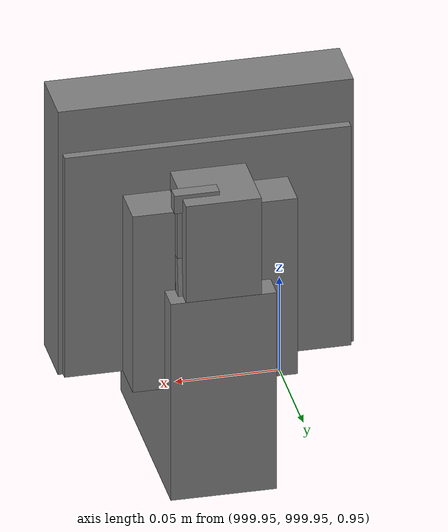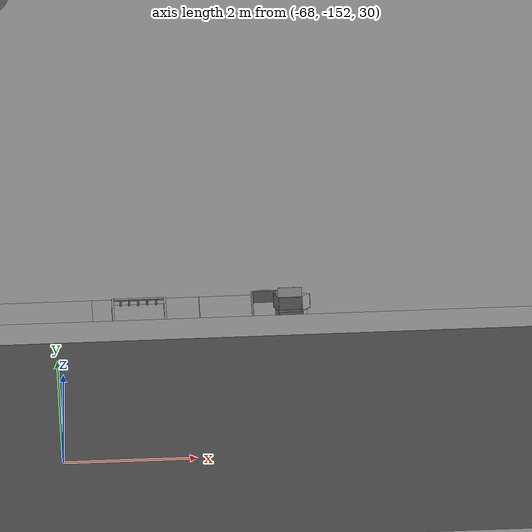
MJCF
<mujoco>
    <option gravity="0.000000000 0.000000000 -9.810000420" timestep="0.0049999999" integrator="implicitfast" density="1.225" viscosity="1.8000001e-05" noslip_iterations="10" iterations="100" sdf_iterations="50">
        <flag multiccd="disable"/>
    </option>
    <size memory="1000M"/>
    <compiler coordinate="local"/>
    <worldbody>
        <light cutoff="30" pos="0 1 1" dir="0 -1 -2"/>
        <light cutoff="30" pos="0 -1 1" dir="0 1 -2"/>
        <body pos="1000.000000000 1000.000000000 1.000000000" euler="0.000000000 0.000000000 180.000000000" name="openloong_gripper_2f85_fix_base_usda_cpu_fan">
            <geom contype="1" conaffinity="1" density="1000" type="box" material="" rgba="0.500000000 0.500000000 0.500000000 1.000000000" solimp="0.899999976 0.949999988 0.001000000" friction="1.000000000 0.005000000 0.000100000" solref="0.020000000 1.000000000" margin="0" condim="3" group="0" pos="0.000000000 0.000000000 0.070034981" quat="0.000000000 0.000000000 0.000000000 1.000000000" size="0.070700005 0.014699999 0.070700005" name="openloong_gripper_2f85_fix_base_usda_geom_B872EB68_3CA6_4612_BB57_A5A988F6397E"/>
            <freejoint name="openloong_gripper_2f85_fix_base_usda_cpu_fan_joint"/>
            <site size="0.005000000 0.005000000 0.005000000" rgba="0.500000000 0.500000000 0.500000000 1.000000000" pos="0.000000000 0.000000000 0.000000000" quat="0.999961913 0.008726535 0.000000000 0.000000000" group="0" type="sphere" name="openloong_gripper_2f85_fix_base_usda_cpu_fancsite"/>
        </body>
        <body pos="-65.802307129 -149.687988281 31.165367126" euler="-26.670814514 -32.487953186 68.373619080" mocap="true" name="spotlight3_SpotLight"/>
        <body pos="1000.000000000 1000.000000000 1.000000000" euler="0.000000000 0.000000000 180.000000000" name="openloong_gripper_2f85_fix_base_usda_battery_01">
            <geom contype="1" conaffinity="1" density="1000" type="box" material="" rgba="0.500000000 0.500000000 0.500000000 1.000000000" solimp="0.899999976 0.949999988 0.001000000" friction="1.000000000 0.005000000 0.000100000" solref="0.020000000 1.000000000" margin="0" condim="3" group="0" pos="-0.011123657 -0.041940309 0.101691343" quat="1.000000000 0.000000000 0.000000000 0.000000000" size="0.010800000 0.003375000 0.004725000" name="openloong_gripper_2f85_fix_base_usda_geom_8E33424C_4B1C_402A_B11D_59065C5A3F72"/>
            <geom contype="1" conaffinity="1" density="1000" type="box" material="" rgba="0.500000000 0.500000000 0.500000000 1.000000000" solimp="0.899999976 0.949999988 0.001000000" friction="1.000000000 0.005000000 0.000100000" solref="0.020000000 1.000000000" margin="0" condim="3" group="0" pos="-0.010876465 -0.044247437 0.047066893" quat="0.998702705 -0.050920475 0.000000000 0.000000000" size="0.009450001 0.002700000 0.024975000" name="openloong_gripper_2f85_fix_base_usda_geom_B6C26446_908F_4F9A_A960_A37E7C377001"/>
            <geom contype="1" conaffinity="1" density="1000" type="box" material="" rgba="0.500000000 0.500000000 0.500000000 1.000000000" solimp="0.899999976 0.949999988 0.001000000" friction="1.000000000 0.005000000 0.000100000" solref="0.020000000 1.000000000" margin="0" condim="3" group="0" pos="-0.001235962 -0.000659180 0.047381196" quat="1.000000000 0.000000000 0.000000000 0.000000000" size="0.039420001 0.039150000 0.047250003" name="openloong_gripper_2f85_fix_base_usda_geom_B45F4F1C_EA55_4B82_B489_B45F40DF8671"/>
            <geom contype="1" conaffinity="1" density="1000" type="box" material="" rgba="0.500000000 0.500000000 0.500000000 1.000000000" solimp="0.899999976 0.949999988 0.001000000" friction="1.000000000 0.005000000 0.000100000" solref="0.020000000 1.000000000" margin="0" condim="3" group="0" pos="-0.010876465 -0.039138794 0.009851727" quat="1.000000000 0.000000000 0.000000000 0.000000000" size="0.009450001 0.010800000 0.013500000" name="openloong_gripper_2f85_fix_base_usda_geom_23187F97_69B9_4FF1_AE3D_EDC7A076CAA5"/>
            <geom contype="1" conaffinity="1" density="1000" type="box" material="" rgba="0.500000000 0.500000000 0.500000000 1.000000000" solimp="0.899999976 0.949999988 0.001000000" friction="1.000000000 0.005000000 0.000100000" solref="0.020000000 1.000000000" margin="0" condim="3" group="0" pos="-0.010876465 -0.041528322 0.071508206" quat="1.000000000 0.000000000 0.000000000 0.000000000" size="0.009450001 0.002700000 0.027000001" name="openloong_gripper_2f85_fix_base_usda_geom_C160F35B_F707_40F3_8FCC_5BE8C5F50E17"/>
            <freejoint name="openloong_gripper_2f85_fix_base_usda_battery_01_joint"/>
            <site size="0.005000000 0.005000000 0.005000000" rgba="0.500000000 0.500000000 0.500000000 1.000000000" pos="0.000000000 0.000000000 0.000000000" quat="0.999961913 0.008726500 0.000000000 0.000000000" group="0" type="sphere" name="openloong_gripper_2f85_fix_base_usda_battery_01site"/>
        </body>
        <body pos="1000.000000000 1000.000000000 1.000000000" euler="0.000000000 0.000000000 180.000000000" name="openloong_gripper_2f85_fix_base_usda_wifi_box">
            <geom contype="1" conaffinity="1" density="1000" type="box" material="" rgba="0.500000000 0.500000000 0.500000000 1.000000000" solimp="0.899999976 0.949999988 0.001000000" friction="1.000000000 0.005000000 0.000100000" solref="0.020000000 1.000000000" margin="0" condim="3" group="0" pos="0.000000000 0.000000000 0.058978677" quat="0.000000000 0.000000047 0.000000000 1.000000000" size="0.068499997 0.018999999 0.059000000" name="openloong_gripper_2f85_fix_base_usda_geom_9D5918AB_39FE_4948_8D0E_E3BC74D1DDE1"/>
            <freejoint name="openloong_gripper_2f85_fix_base_usda_wifi_box_joint"/>
            <site size="0.005000000 0.005000000 0.005000000" rgba="0.500000000 0.500000000 0.500000000 1.000000000" pos="0.000000000 0.000000000 0.000000000" quat="0.999961913 0.008726500 0.000000000 0.000000000" group="0" type="sphere" name="openloong_gripper_2f85_fix_base_usda_wifi_boxsite"/>
        </body>
        <body pos="-65.904838562 -149.191238403 31.171899796" euler="-10.038461685 -53.092250824 -24.711847305" mocap="true" name="spotlight6_SpotLight"/>
        <body pos="1000.000000000 1000.000000000 1.000000000" euler="0.000011953 0.000005123 -179.999984741" name="openloong_gripper_2f85_fix_base_usda_intel_box">
            <geom contype="1" conaffinity="1" density="1000" type="box" material="" rgba="0.500000000 0.500000000 0.500000000 1.000000000" solimp="0.899999976 0.949999988 0.001000000" friction="1.000000000 0.005000000 0.000100000" solref="0.020000000 1.000000000" margin="0" condim="3" group="0" pos="0.000000000 -0.000067139 0.000082284" quat="0.707106709 0.000000225 0.000000253 0.707106650" size="0.052800003 0.025300000 0.052800003" name="openloong_gripper_2f85_fix_base_usda_geom_70F4B453_632E_4E45_97BE_8EBA625EDCC4"/>
            <freejoint name="openloong_gripper_2f85_fix_base_usda_intel_box_joint"/>
            <site size="0.005000000 0.005000000 0.005000000" rgba="0.500000000 0.500000000 0.500000000 1.000000000" pos="0.000000000 0.000000000 0.000000000" quat="0.999961913 0.008726500 0.000000000 0.000000000" group="0" type="sphere" name="openloong_gripper_2f85_fix_base_usda_intel_boxsite"/>
        </body>
        <body pos="1000.000000000 999.999938965 1.000000000" euler="0.000000000 0.000000000 180.000000000" name="openloong_gripper_2f85_fix_base_usda_intelcore_i5">
            <geom contype="1" conaffinity="1" density="1000" type="box" material="" rgba="0.500000000 0.500000000 0.500000000 1.000000000" solimp="0.899999976 0.949999988 0.001000000" friction="1.000000000 0.005000000 0.000100000" solref="0.020000000 1.000000000" margin="0" condim="3" group="0" pos="0.000000000 0.000000000 0.051722717" quat="0.707106709 0.000000000 0.000000000 -0.707106769" size="0.052800000 0.018080002 0.052800000" name="openloong_gripper_2f85_fix_base_usda_geom_8B0FB008_E28F_4BBC_B964_2DCC74CCD55D"/>
            <freejoint name="openloong_gripper_2f85_fix_base_usda_intelcore_i5_joint"/>
            <site size="0.005000000 0.005000000 0.005000000" rgba="0.500000000 0.500000000 0.500000000 1.000000000" pos="0.000000000 0.000000000 0.000000000" quat="0.999961913 0.008726534 0.000000000 0.000000000" group="0" type="sphere" name="openloong_gripper_2f85_fix_base_usda_intelcore_i5site"/>
        </body>
        <body pos="-65.829589844 -149.589797974 31.164785385" euler="-166.937728882 -44.758724213 24.732488632" mocap="true" name="spotlight4_SpotLight"/>
        <body pos="-64.866622925 -149.383972168 30.183746338" euler="89.999984741 89.999946594 0.000000000" name="openloong_gripper_2f85_fix_base_usda_bluebox_01">
            <geom contype="1" conaffinity="1" density="1000" type="box" material="" rgba="0.500000000 0.500000000 0.500000000 1.000000000" solimp="0.899999976 0.949999988 0.001000000" friction="1.000000000 0.005000000 0.000100000" solref="0.020000000 1.000000000" margin="0" condim="3" group="0" pos="0.276580811 0.187225342 0.000068665" quat="0.707106948 0.000077471 0.707106352 0.000077486" size="0.100000001 0.057999998 0.010000000" name="openloong_gripper_2f85_fix_base_usda_geom_79073ECB_A9D3_422F_8A98_0CF6D7E7D2B8"/>
            <geom contype="1" conaffinity="1" density="1000" type="box" material="" rgba="0.500000000 0.500000000 0.500000000 1.000000000" solimp="0.899999976 0.949999988 0.001000000" friction="1.000000000 0.005000000 0.000100000" solref="0.020000000 1.000000000" margin="0" condim="3" group="0" pos="0.000000000 0.002883911 0.000000000" quat="0.999999881 0.000000000 0.000000000 0.000000000" size="0.254000008 0.003000000 0.172000006" name="openloong_gripper_2f85_fix_base_usda_geom_02BB97FA_03B8_47B2_8F47_58FD6A69171C"/>
            <geom contype="1" conaffinity="1" density="1000" type="box" material="" rgba="0.500000000 0.500000000 0.500000000 1.000000000" solimp="0.899999976 0.949999988 0.001000000" friction="1.000000000 0.005000000 0.000100000" solref="0.020000000 1.000000000" margin="0" condim="3" group="0" pos="0.000000000 0.124874115 0.173484802" quat="0.999796331 0.020176515 -0.000000015 0.000000030" size="0.259999990 0.119999997 0.007000000" name="openloong_gripper_2f85_fix_base_usda_geom_BE3D10E4_BEB0_4E30_A2B7_36D9FF36EBBB"/>
            <geom contype="1" conaffinity="1" density="1000" type="box" material="" rgba="0.500000000 0.500000000 0.500000000 1.000000000" solimp="0.899999976 0.949999988 0.001000000" friction="1.000000000 0.005000000 0.000100000" solref="0.020000000 1.000000000" margin="0" condim="3" group="0" pos="0.000000000 0.124874115 -0.173469543" quat="0.999796331 -0.020176545 -0.000000015 0.000000000" size="0.259999990 0.119999997 0.007000000" name="openloong_gripper_2f85_fix_base_usda_geom_BC69EF7F_80BF_4FB1_A7FA_6AA065B70ADB"/>
            <geom contype="1" conaffinity="1" density="1000" type="box" material="" rgba="0.500000000 0.500000000 0.500000000 1.000000000" solimp="0.899999976 0.949999988 0.001000000" friction="1.000000000 0.005000000 0.000100000" solref="0.020000000 1.000000000" margin="0" condim="3" group="0" pos="0.000000000 0.214008331 0.188980103" quat="0.999912977 0.013176724 0.000000015 0.000000000" size="0.259999990 0.029999999 0.012500000" name="openloong_gripper_2f85_fix_base_usda_geom_E5106F6C_8BF3_4D27_9CF0_9EDD772468E6"/>
            <geom contype="1" conaffinity="1" density="1000" type="box" material="" rgba="0.500000000 0.500000000 0.500000000 1.000000000" solimp="0.899999976 0.949999988 0.001000000" friction="1.000000000 0.005000000 0.000100000" solref="0.020000000 1.000000000" margin="0" condim="3" group="0" pos="-0.258361816 0.125289917 0.001876831" quat="0.702796936 -0.020792112 0.710783124 0.020769298" size="0.189999998 0.119999997 0.009000000" name="openloong_gripper_2f85_fix_base_usda_geom_6AD78FA5_3DE5_4C24_A956_6A865B116CDE"/>
            <geom contype="1" conaffinity="1" density="1000" type="box" material="" rgba="0.500000000 0.500000000 0.500000000 1.000000000" solimp="0.899999976 0.949999988 0.001000000" friction="1.000000000 0.005000000 0.000100000" solref="0.020000000 1.000000000" margin="0" condim="3" group="0" pos="0.000000000 0.214008331 -0.188980103" quat="0.999912977 -0.013176769 0.000000030 0.000000015" size="0.259999990 0.029999999 0.012500000" name="openloong_gripper_2f85_fix_base_usda_geom_B7AE0760_9F8E_45F9_A8CC_81520E914AE5"/>
            <geom contype="1" conaffinity="1" density="1000" type="box" material="" rgba="0.500000000 0.500000000 0.500000000 1.000000000" solimp="0.899999976 0.949999988 0.001000000" friction="1.000000000 0.005000000 0.000100000" solref="0.020000000 1.000000000" margin="0" condim="3" group="0" pos="-0.276611328 0.187225342 0.000068665" quat="0.707106650 0.000077441 0.707106709 0.000077456" size="0.100000001 0.057999998 0.010000000" name="openloong_gripper_2f85_fix_base_usda_geom_922BB4D1_3DE9_415A_8599_61C9FAF44721"/>
            <geom contype="1" conaffinity="1" density="1000" type="box" material="" rgba="0.500000000 0.500000000 0.500000000 1.000000000" solimp="0.899999976 0.949999988 0.001000000" friction="1.000000000 0.005000000 0.000100000" solref="0.020000000 1.000000000" margin="0" condim="3" group="0" pos="0.258331299 0.125289917 0.001876831" quat="0.702851415 0.018856421 0.710823774 -0.019329369" size="0.189999998 0.119999997 0.009000000" name="openloong_gripper_2f85_fix_base_usda_geom_207F7A4F_46C3_4FDA_8BE0_9EE9B6F2869F"/>
            <freejoint name="openloong_gripper_2f85_fix_base_usda_bluebox_01_joint"/>
            <site size="0.005000000 0.005000000 0.005000000" rgba="0.500000000 0.500000000 0.500000000 1.000000000" pos="0.000000000 0.000000000 0.000000000" quat="0.999961913 0.008726534 0.000000000 0.000000000" group="0" type="sphere" name="openloong_gripper_2f85_fix_base_usda_bluebox_01site"/>
        </body>
        <body pos="-64.496299744 -149.491867065 30.235729218" euler="0.000000000 0.000000000 89.999946594" name="openloong_gripper_2f85_fix_base_usda_cardboardbox_01">
            <geom contype="1" conaffinity="1" density="1000" type="box" material="" rgba="0.500000000 0.500000000 0.500000000 1.000000000" solimp="0.899999976 0.949999988 0.001000000" friction="1.000000000 0.005000000 0.000100000" solref="0.020000000 1.000000000" margin="0" condim="3" group="0" pos="-0.003166199 -0.004086494 0.005052090" quat="1.000000000 0.000000000 0.000000000 0.000000000" size="0.142499998 0.177500010 0.005000000" name="openloong_gripper_2f85_fix_base_usda_geom_C3E103DD_B7C8_4BFA_92F2_712591016906"/>
            <geom contype="1" conaffinity="1" density="1000" type="box" material="" rgba="0.500000000 0.500000000 0.500000000 1.000000000" solimp="0.899999976 0.949999988 0.001000000" friction="1.000000000 0.005000000 0.000100000" solref="0.020000000 1.000000000" margin="0" condim="3" group="0" pos="-0.003166199 0.170316696 0.150570869" quat="1.000000000 0.000000000 0.000000000 0.000000000" size="0.142499998 0.005000000 0.149999991" name="openloong_gripper_2f85_fix_base_usda_geom_B25E5D18_5F82_46CA_BE40_9DDA08C1898E"/>
            <geom contype="1" conaffinity="1" density="1000" type="box" material="" rgba="0.500000000 0.500000000 0.500000000 1.000000000" solimp="0.899999976 0.949999988 0.001000000" friction="1.000000000 0.005000000 0.000100000" solref="0.020000000 1.000000000" margin="0" condim="3" group="0" pos="-0.147399902 -0.005307198 0.150570869" quat="1.000000000 0.000000000 0.000000000 0.000000000" size="0.005000000 0.177500010 0.149999991" name="openloong_gripper_2f85_fix_base_usda_geom_1945D73F_F343_4C3B_98F7_AEA2FA89D570"/>
            <geom contype="1" conaffinity="1" density="1000" type="box" material="" rgba="0.500000000 0.500000000 0.500000000 1.000000000" solimp="0.899999976 0.949999988 0.001000000" friction="1.000000000 0.005000000 0.000100000" solref="0.020000000 1.000000000" margin="0" condim="3" group="0" pos="0.140275955 -0.005307198 0.150570869" quat="1.000000000 0.000000000 0.000000000 0.000000000" size="0.005000000 0.177500010 0.149999991" name="openloong_gripper_2f85_fix_base_usda_geom_EE7E90D5_FF90_4803_AFC0_90E1AF07D46C"/>
            <geom contype="1" conaffinity="1" density="1000" type="box" material="" rgba="0.500000000 0.500000000 0.500000000 1.000000000" solimp="0.899999976 0.949999988 0.001000000" friction="1.000000000 0.005000000 0.000100000" solref="0.020000000 1.000000000" margin="0" condim="3" group="0" pos="-0.003166199 -0.181550980 0.150570869" quat="1.000000000 0.000000000 0.000000000 0.000000000" size="0.142499998 0.005000000 0.149999991" name="openloong_gripper_2f85_fix_base_usda_geom_F3BA8839_B90A_47D4_A30F_FFA994613C26"/>
            <freejoint name="openloong_gripper_2f85_fix_base_usda_cardboardbox_01_joint"/>
            <site size="0.005000000 0.005000000 0.005000000" rgba="0.500000000 0.500000000 0.500000000 1.000000000" pos="0.000000000 0.000000000 0.000000000" quat="0.999961913 0.008726535 0.000000000 0.000000000" group="0" type="sphere" name="openloong_gripper_2f85_fix_base_usda_site_2E8BE4F3_FE95_467A_8398_002C243FB067"/>
            <body pos="0.139160156 -0.004048347 0.301930904" euler="-179.999954224 49.383502960 179.999954224" name="openloong_gripper_2f85_fix_base_usda_A1_006">
                <geom contype="1" conaffinity="1" density="1000" type="box" material="" rgba="0.500000000 0.500000000 0.500000000 1.000000000" solimp="0.899999976 0.949999988 0.001000000" friction="1.000000000 0.005000000 0.000100000" solref="0.020000000 1.000000000" margin="0" condim="3" group="0" pos="-0.071587563 0.000009537 0.001745224" quat="0.999999881 0.000000000 0.000000000 0.000000000" size="0.071249999 0.179999992 0.002500000" name="openloong_gripper_2f85_fix_base_usda_geom_374E26B4_233C_458C_B58A_9AAFEEAB86D6"/>
                <joint armature="0" stiffness="0.07" damping="0.0099999998" axis="0.000000 1.000000 0.000000" type="hinge" name="openloong_gripper_2f85_fix_base_usda_A1_006"/>
            </body>
            <body pos="-0.145902634 -0.004086494 0.301938057" euler="-180.000000000 -60.000011444 -180.000000000" name="openloong_gripper_2f85_fix_base_usda_A2_006">
                <geom contype="1" conaffinity="1" density="1000" type="box" material="" rgba="0.500000000 0.500000000 0.500000000 1.000000000" solimp="0.899999976 0.949999988 0.001000000" friction="1.000000000 0.005000000 0.000100000" solref="0.020000000 1.000000000" margin="0" condim="3" group="0" pos="0.071268082 0.000009537 0.002717972" quat="0.000002921 0.000000000 -0.000000030 0.999999881" size="0.071249999 0.179999992 0.002500000" name="openloong_gripper_2f85_fix_base_usda_geom_D1A85446_0D1F_49C5_A1DE_242701040732"/>
                <joint armature="0" stiffness="0.07" damping="0.0099999998" axis="0.000000 1.000000 0.000000" type="hinge" name="openloong_gripper_2f85_fix_base_usda_A2_006"/>
            </body>
            <body pos="-0.003385544 0.175991058 0.301930904" euler="-125.858116150 -0.000004561 0.000002331" name="openloong_gripper_2f85_fix_base_usda_B2_006">
                <geom contype="1" conaffinity="1" density="1000" type="box" material="" rgba="0.500000000 0.500000000 0.500000000 1.000000000" solimp="0.899999976 0.949999988 0.001000000" friction="1.000000000 0.005000000 0.000100000" solref="0.020000000 1.000000000" margin="0" condim="3" group="0" pos="0.000009537 -0.070939064 -0.002470016" quat="0.999614120 0.027776197 -0.000000015 0.000000030" size="0.137500003 0.064999998 0.005000000" name="openloong_gripper_2f85_fix_base_usda_geom_322E9C81_1D22_4051_99C9_09B3467FFD9E"/>
                <joint armature="0" stiffness="0.07" damping="0.0099999998" axis="1.000000 0.000000 0.000000" type="hinge" name="openloong_gripper_2f85_fix_base_usda_B2_006"/>
            </body>
            <body pos="-0.003385544 -0.184140205 0.301938057" euler="147.805557251 0.000000000 0.000000000" name="openloong_gripper_2f85_fix_base_usda_B1_006">
                <geom contype="1" conaffinity="1" density="1000" type="box" material="" rgba="0.500000000 0.500000000 0.500000000 1.000000000" solimp="0.899999976 0.949999988 0.001000000" friction="1.000000000 0.005000000 0.000100000" solref="0.020000000 1.000000000" margin="0" condim="3" group="0" pos="-0.000028610 0.070202351 -0.002703667" quat="0.999614179 -0.027776167 0.000000000 0.000000000" size="0.137500003 0.064999998 0.005000000" name="openloong_gripper_2f85_fix_base_usda_geom_929E39F1_ED0D_45AA_AF2D_29CC20B65A1B"/>
                <joint armature="0" stiffness="0.07" damping="0.0099999998" axis="1.000000 0.000000 0.000000" type="hinge" name="openloong_gripper_2f85_fix_base_usda_B1_006"/>
            </body>
        </body>
        <body pos="-65.882858276 -149.481979370 30.229999542" euler="-64.487716675 0.000000000 0.000000000" name="openloong_gripper_2f85_fix_base_usda_Barcode">
            <geom contype="1" conaffinity="1" density="1000" type="box" material="" rgba="0.500000000 0.500000000 0.500000000 1.000000000" solimp="0.899999976 0.949999988 0.001000000" friction="1.000000000 0.005000000 0.000100000" solref="0.020000000 1.000000000" margin="0" condim="3" group="0" pos="0.000000000 0.013038635 0.001419067" quat="0.000000000 0.000000000 0.000000000 1.000000119" size="0.034000002 0.010000000 0.017999999" name="openloong_gripper_2f85_fix_base_usda_geom_5D18B3DD_0201_4DE6_9C19_DBC135C4282F"/>
            <geom contype="1" conaffinity="1" density="1000" type="box" material="" rgba="0.500000000 0.500000000 0.500000000 1.000000000" solimp="0.899999976 0.949999988 0.001000000" friction="1.000000000 0.005000000 0.000100000" solref="0.020000000 1.000000000" margin="0" condim="3" group="0" pos="0.000000000 -0.035301208 -0.007095337" quat="0.000000000 0.000000000 -0.043619365 0.999048233" size="0.028999999 0.010000000 0.020000000" name="openloong_gripper_2f85_fix_base_usda_geom_9760E533_1CCA_4B2C_984F_B23C65BAFACB"/>
            <geom contype="1" conaffinity="1" density="1000" type="box" material="" rgba="0.500000000 0.500000000 0.500000000 1.000000000" solimp="0.899999976 0.949999988 0.001000000" friction="1.000000000 0.005000000 0.000100000" solref="0.020000000 1.000000000" margin="0" condim="3" group="0" pos="0.000000000 -0.043411255 -0.011749268" quat="0.922262907 0.386563420 0.000000000 0.000000000" size="0.026000001 0.010000000 0.020000000" name="openloong_gripper_2f85_fix_base_usda_geom_010AB240_80EC_4275_A1CA_1B34B04D7BF4"/>
            <geom contype="1" conaffinity="1" density="1000" type="box" material="" rgba="0.500000000 0.500000000 0.500000000 1.000000000" solimp="0.899999976 0.949999988 0.001000000" friction="1.000000000 0.005000000 0.000100000" solref="0.020000000 1.000000000" margin="0" condim="3" group="0" pos="0.000000000 -0.016967773 -0.031860352" quat="0.000000000 0.000000000 0.000000000 1.000000119" size="0.008000000 0.010000000 0.013000000" name="openloong_gripper_2f85_fix_base_usda_geom_C6AFEA6E_8C52_4AC8_9F65_2B08E9496655"/>
            <geom contype="1" conaffinity="1" density="1000" type="box" material="" rgba="0.500000000 0.500000000 0.500000000 1.000000000" solimp="0.899999976 0.949999988 0.001000000" friction="1.000000000 0.005000000 0.000100000" solref="0.020000000 1.000000000" margin="0" condim="3" group="0" pos="0.000000000 -0.001869202 0.000312805" quat="0.953716993 0.300705761 0.000000000 0.000000000" size="0.032000002 0.010000000 0.018999999" name="openloong_gripper_2f85_fix_base_usda_geom_222EEB6B_2886_4F8F_AEF5_2E1E8BA4A397"/>
            <geom contype="1" conaffinity="1" density="1000" type="box" material="" rgba="0.500000000 0.500000000 0.500000000 1.000000000" solimp="0.899999976 0.949999988 0.001000000" friction="1.000000000 0.005000000 0.000100000" solref="0.020000000 1.000000000" margin="0" condim="3" group="0" pos="0.000000000 -0.019531250 -0.003173828" quat="0.953716993 0.300705761 0.000000000 0.000000000" size="0.030999999 0.010000000 0.020000000" name="openloong_gripper_2f85_fix_base_usda_geom_8F120EFF_C9C0_47AE_978D_14BB9827F215"/>
            <geom contype="1" conaffinity="1" density="1000" type="box" material="" rgba="0.500000000 0.500000000 0.500000000 1.000000000" solimp="0.899999976 0.949999988 0.001000000" friction="1.000000000 0.005000000 0.000100000" solref="0.020000000 1.000000000" margin="0" condim="3" group="0" pos="0.000000000 -0.035301208 -0.007095337" quat="0.953716993 0.300705761 0.000000000 0.000000000" size="0.028999999 0.010000000 0.020000000" name="openloong_gripper_2f85_fix_base_usda_geom_40E39631_726A_4FC4_B3DA_C84A0BCDBD9E"/>
            <geom contype="1" conaffinity="1" density="1000" type="box" material="" rgba="0.500000000 0.500000000 0.500000000 1.000000000" solimp="0.899999976 0.949999988 0.001000000" friction="1.000000000 0.005000000 0.000100000" solref="0.020000000 1.000000000" margin="0" condim="3" group="0" pos="0.000000000 -0.042617798 -0.071121216" quat="0.000000000 0.000000000 0.000000000 1.000000119" size="0.013000000 0.021000000 0.059999999" name="openloong_gripper_2f85_fix_base_usda_geom_BCE10E74_A1C3_41AE_B913_6D58E33E3C96"/>
            <freejoint name="openloong_gripper_2f85_fix_base_usda_Barcode_joint"/>
            <site size="0.005000000 0.005000000 0.005000000" rgba="0.500000000 0.500000000 0.500000000 1.000000000" pos="0.000000000 0.000000000 0.000000000" quat="1.000000000 0.000000000 0.000000000 0.000000000" group="0" type="sphere" name="openloong_gripper_2f85_fix_base_usda_Barcode_site"/>
        </body>
        <body pos="-66.745018005 -149.392349243 30.184000015" euler="0.000000000 0.000000000 89.999946594" name="[22333315341574]_Basket_01">
            <geom contype="1" conaffinity="1" density="1000" type="box" material="" rgba="0.500000000 0.500000000 0.500000000 1.000000000" solimp="0.899999976 0.949999988 0.001000000" friction="1.000000000 0.005000000 0.000100000" solref="0.020000000 1.000000000" margin="0" condim="3" group="0" pos="-0.052425385 0.389207840 0.089787483" quat="0.707107008 0.000000000 0.000000000 0.707106411" size="0.014249999 0.014249999 0.059999999" name="[22333315341574]_geom_585BE38C_A891_43C7_9EF5_D842A060844B"/>
            <geom contype="1" conaffinity="1" density="1000" type="box" material="" rgba="0.500000000 0.500000000 0.500000000 1.000000000" solimp="0.899999976 0.949999988 0.001000000" friction="1.000000000 0.005000000 0.000100000" solref="0.020000000 1.000000000" margin="0" condim="3" group="0" pos="0.264015198 -0.133043289 0.089787483" quat="0.707107008 0.000000000 0.000000000 0.707106411" size="0.014249999 0.014249999 0.059999999" name="[22333315341574]_geom_E21D3A85_A6D0_40DE_BE7C_AE9E73EB0C31"/>
            <geom contype="1" conaffinity="1" density="1000" type="box" material="" rgba="0.500000000 0.500000000 0.500000000 1.000000000" solimp="0.899999976 0.949999988 0.001000000" friction="1.000000000 0.005000000 0.000100000" solref="0.020000000 1.000000000" margin="0" condim="3" group="0" pos="-0.264015198 -0.265548706 0.089793205" quat="0.707107008 0.000000000 0.000000000 0.707106411" size="0.014249999 0.014249999 0.059999999" name="[22333315341574]_geom_2C5C9169_3F1D_4408_B45D_5F5D6F06DE39"/>
            <geom contype="1" conaffinity="1" density="1000" type="box" material="" rgba="0.500000000 0.500000000 0.500000000 1.000000000" solimp="0.899999976 0.949999988 0.001000000" friction="1.000000000 0.005000000 0.000100000" solref="0.020000000 1.000000000" margin="0" condim="3" group="0" pos="-0.160263062 -0.389322281 0.089793205" quat="0.707107008 0.000000000 0.000000000 0.707106411" size="0.014249999 0.014249999 0.059999999" name="[22333315341574]_geom_F995C676_A4F1_48D0_BC06_C5238EEFA07D"/>
            <geom contype="1" conaffinity="1" density="1000" type="box" material="" rgba="0.500000000 0.500000000 0.500000000 1.000000000" solimp="0.899999976 0.949999988 0.001000000" friction="1.000000000 0.005000000 0.000100000" solref="0.020000000 1.000000000" margin="0" condim="3" group="0" pos="0.162265778 -0.389322281 0.089787483" quat="0.707107008 0.000000000 0.000000000 0.707106411" size="0.014249999 0.014249999 0.059999999" name="[22333315341574]_geom_B964B692_7957_4292_A18B_A2FC9B234214"/>
            <geom contype="1" conaffinity="1" density="1000" type="box" material="" rgba="0.500000000 0.500000000 0.500000000 1.000000000" solimp="0.899999976 0.949999988 0.001000000" friction="1.000000000 0.005000000 0.000100000" solref="0.020000000 1.000000000" margin="0" condim="3" group="0" pos="0.264015198 0.389207840 0.089787483" quat="0.707107008 0.000000000 0.000000000 0.707106411" size="0.014249999 0.014249999 0.059999999" name="[22333315341574]_geom_D62FEFA3_E469_4093_B7F7_53E7C4154196"/>
            <geom contype="1" conaffinity="1" density="1000" type="box" material="" rgba="0.500000000 0.500000000 0.500000000 1.000000000" solimp="0.899999976 0.949999988 0.001000000" friction="1.000000000 0.005000000 0.000100000" solref="0.020000000 1.000000000" margin="0" condim="3" group="0" pos="-0.264015198 -0.133043289 0.089793205" quat="0.707107008 0.000000000 0.000000000 0.707106411" size="0.014249999 0.014249999 0.059999999" name="[22333315341574]_geom_3E6C8A4F_4B27_438B_AA27_9796098BA471"/>
            <geom contype="1" conaffinity="1" density="1000" type="box" material="" rgba="0.500000000 0.500000000 0.500000000 1.000000000" solimp="0.899999976 0.949999988 0.001000000" friction="1.000000000 0.005000000 0.000100000" solref="0.020000000 1.000000000" margin="0" condim="3" group="0" pos="-0.264026642 0.269256592 0.089793205" quat="0.707107008 0.000000000 0.000000000 0.707106411" size="0.014249999 0.014249999 0.059999999" name="[22333315341574]_geom_AC473A0C_1D54_4684_AB27_D72C5329469F"/>
            <geom contype="1" conaffinity="1" density="1000" type="box" material="" rgba="0.500000000 0.500000000 0.500000000 1.000000000" solimp="0.899999976 0.949999988 0.001000000" friction="1.000000000 0.005000000 0.000100000" solref="0.020000000 1.000000000" margin="0" condim="3" group="0" pos="0.054462433 0.389207840 0.089787483" quat="0.707107008 0.000000000 0.000000000 0.707106411" size="0.014249999 0.014249999 0.059999999" name="[22333315341574]_geom_CEE492AA_C66A_4B56_8C63_1BF1522DFAB4"/>
            <geom contype="1" conaffinity="1" density="1000" type="box" material="" rgba="0.500000000 0.500000000 0.500000000 1.000000000" solimp="0.899999976 0.949999988 0.001000000" friction="1.000000000 0.005000000 0.000100000" solref="0.020000000 1.000000000" margin="0" condim="3" group="0" pos="0.054462433 -0.389322281 0.089787483" quat="0.707107008 0.000000000 0.000000000 0.707106411" size="0.014249999 0.014249999 0.059999999" name="[22333315341574]_geom_00A921A4_768C_4429_A538_99164B1FFEA9"/>
            <geom contype="1" conaffinity="1" density="1000" type="box" material="" rgba="0.500000000 0.500000000 0.500000000 1.000000000" solimp="0.899999976 0.949999988 0.001000000" friction="1.000000000 0.005000000 0.000100000" solref="0.020000000 1.000000000" margin="0" condim="3" group="0" pos="0.264015198 0.269256592 0.089793205" quat="0.707107008 0.000000000 0.000000000 0.707106411" size="0.014249999 0.014249999 0.059999999" name="[22333315341574]_geom_1944BBAA_4DF1_4A58_B54F_BFDE0E7E382F"/>
            <geom contype="1" conaffinity="1" density="1000" type="box" material="" rgba="0.500000000 0.500000000 0.500000000 1.000000000" solimp="0.899999976 0.949999988 0.001000000" friction="1.000000000 0.005000000 0.000100000" solref="0.020000000 1.000000000" margin="0" condim="3" group="0" pos="0.264015198 -0.389322281 0.089787483" quat="0.707107008 0.000000000 0.000000000 0.707106411" size="0.014249999 0.014249999 0.059999999" name="[22333315341574]_geom_F3B694CF_62E7_44D3_ACD4_C692A8DF7410"/>
            <geom contype="1" conaffinity="1" density="1000" type="box" material="" rgba="0.500000000 0.500000000 0.500000000 1.000000000" solimp="0.899999976 0.949999988 0.001000000" friction="1.000000000 0.005000000 0.000100000" solref="0.020000000 1.000000000" margin="0" condim="3" group="0" pos="0.000000000 0.000000000 0.015998840" quat="0.707107008 0.000000000 0.000000000 0.707106411" size="0.403499991 0.279000014 0.015750000" name="[22333315341574]_geom_7E1A66A6_5191_4267_9093_FC49E0B17005"/>
            <geom contype="1" conaffinity="1" density="1000" type="box" material="" rgba="0.500000000 0.500000000 0.500000000 1.000000000" solimp="0.899999976 0.949999988 0.001000000" friction="1.000000000 0.005000000 0.000100000" solref="0.020000000 1.000000000" margin="0" condim="3" group="0" pos="0.000000000 -0.389476776 0.163619041" quat="0.707107008 0.000000000 0.000000000 0.707106411" size="0.015000000 0.277500004 0.015750000" name="[22333315341574]_geom_77520C65_CA0F_4D17_A860_822C6068DF4D"/>
            <geom contype="1" conaffinity="1" density="1000" type="box" material="" rgba="0.500000000 0.500000000 0.500000000 1.000000000" solimp="0.899999976 0.949999988 0.001000000" friction="1.000000000 0.005000000 0.000100000" solref="0.020000000 1.000000000" margin="0" condim="3" group="0" pos="0.162265778 0.389207840 0.089787483" quat="0.707107008 0.000000000 0.000000000 0.707106411" size="0.014249999 0.014249999 0.059999999" name="[22333315341574]_geom_04531889_2B04_4DC4_88FF_29F2D9B3D511"/>
            <geom contype="1" conaffinity="1" density="1000" type="box" material="" rgba="0.500000000 0.500000000 0.500000000 1.000000000" solimp="0.899999976 0.949999988 0.001000000" friction="1.000000000 0.005000000 0.000100000" solref="0.020000000 1.000000000" margin="0" condim="3" group="0" pos="0.000000000 0.389471054 0.163619041" quat="0.707107008 0.000000000 0.000000000 0.707106411" size="0.015000000 0.277500004 0.015750000" name="[22333315341574]_geom_79E99BAC_CDAB_473C_821D_AF2C76E84A13"/>
            <geom contype="1" conaffinity="1" density="1000" type="box" material="" rgba="0.500000000 0.500000000 0.500000000 1.000000000" solimp="0.899999976 0.949999988 0.001000000" friction="1.000000000 0.005000000 0.000100000" solref="0.020000000 1.000000000" margin="0" condim="3" group="0" pos="-0.263511658 0.000000000 0.163619041" quat="0.707107008 0.000000000 0.000000000 0.707106411" size="0.403499991 0.015000000 0.015750000" name="[22333315341574]_geom_AE255672_80CA_4508_A1C2_8BCFDB9028DA"/>
            <geom contype="1" conaffinity="1" density="1000" type="box" material="" rgba="0.500000000 0.500000000 0.500000000 1.000000000" solimp="0.899999976 0.949999988 0.001000000" friction="1.000000000 0.005000000 0.000100000" solref="0.020000000 1.000000000" margin="0" condim="3" group="0" pos="-0.264015198 0.141334534 0.089793205" quat="0.707107008 0.000000000 0.000000000 0.707106411" size="0.014249999 0.014249999 0.059999999" name="[22333315341574]_geom_08E91698_C1D4_48B1_8EF5_50D45CFD651F"/>
            <geom contype="1" conaffinity="1" density="1000" type="box" material="" rgba="0.500000000 0.500000000 0.500000000 1.000000000" solimp="0.899999976 0.949999988 0.001000000" friction="1.000000000 0.005000000 0.000100000" solref="0.020000000 1.000000000" margin="0" condim="3" group="0" pos="0.264015198 -0.265548706 0.089787483" quat="0.707107008 0.000000000 0.000000000 0.707106411" size="0.014249999 0.014249999 0.059999999" name="[22333315341574]_geom_16D8F5A7_5416_4823_A542_820556AED147"/>
            <geom contype="1" conaffinity="1" density="1000" type="box" material="" rgba="0.500000000 0.500000000 0.500000000 1.000000000" solimp="0.899999976 0.949999988 0.001000000" friction="1.000000000 0.005000000 0.000100000" solref="0.020000000 1.000000000" margin="0" condim="3" group="0" pos="-0.160263062 0.389207840 0.089787483" quat="0.707107008 0.000000000 0.000000000 0.707106411" size="0.014249999 0.014249999 0.059999999" name="[22333315341574]_geom_AFEB0A30_2B8D_43BC_BB39_AD20A0FA61C9"/>
            <geom contype="1" conaffinity="1" density="1000" type="box" material="" rgba="0.500000000 0.500000000 0.500000000 1.000000000" solimp="0.899999976 0.949999988 0.001000000" friction="1.000000000 0.005000000 0.000100000" solref="0.020000000 1.000000000" margin="0" condim="3" group="0" pos="-0.052425385 -0.389322281 0.089787483" quat="0.707107008 0.000000000 0.000000000 0.707106411" size="0.014249999 0.014249999 0.059999999" name="[22333315341574]_geom_CAAFC8C7_FF51_4E55_B128_99765A4EACBC"/>
            <geom contype="1" conaffinity="1" density="1000" type="box" material="" rgba="0.500000000 0.500000000 0.500000000 1.000000000" solimp="0.899999976 0.949999988 0.001000000" friction="1.000000000 0.005000000 0.000100000" solref="0.020000000 1.000000000" margin="0" condim="3" group="0" pos="-0.264026642 -0.389322281 0.089793205" quat="0.707107008 0.000000000 0.000000000 0.707106411" size="0.014249999 0.014249999 0.059999999" name="[22333315341574]_geom_0F938B04_A317_4D1B_9635_B03DF3780C73"/>
            <geom contype="1" conaffinity="1" density="1000" type="box" material="" rgba="0.500000000 0.500000000 0.500000000 1.000000000" solimp="0.899999976 0.949999988 0.001000000" friction="1.000000000 0.005000000 0.000100000" solref="0.020000000 1.000000000" margin="0" condim="3" group="0" pos="0.264015198 0.141334534 0.089787483" quat="0.707107008 0.000000000 0.000000000 0.707106411" size="0.014249999 0.014249999 0.059999999" name="[22333315341574]_geom_A2A94BFD_BF3F_46D2_B518_7EFB9CA35FA6"/>
            <geom contype="1" conaffinity="1" density="1000" type="box" material="" rgba="0.500000000 0.500000000 0.500000000 1.000000000" solimp="0.899999976 0.949999988 0.001000000" friction="1.000000000 0.005000000 0.000100000" solref="0.020000000 1.000000000" margin="0" condim="3" group="0" pos="-0.264015198 0.389207840 0.089793205" quat="0.707107008 0.000000000 0.000000000 0.707106411" size="0.014249999 0.014249999 0.059999999" name="[22333315341574]_geom_88CE2D5F_F173_47F7_B3D6_AD9799E35F86"/>
            <geom contype="1" conaffinity="1" density="1000" type="box" material="" rgba="0.500000000 0.500000000 0.500000000 1.000000000" solimp="0.899999976 0.949999988 0.001000000" friction="1.000000000 0.005000000 0.000100000" solref="0.020000000 1.000000000" margin="0" condim="3" group="0" pos="0.264015198 0.004480362 0.089787483" quat="0.707107008 0.000000000 0.000000000 0.707106411" size="0.014249999 0.014249999 0.059999999" name="[22333315341574]_geom_CA206C02_EEAF_4D49_B2F6_FD066D5C92AD"/>
            <geom contype="1" conaffinity="1" density="1000" type="box" material="" rgba="0.500000000 0.500000000 0.500000000 1.000000000" solimp="0.899999976 0.949999988 0.001000000" friction="1.000000000 0.005000000 0.000100000" solref="0.020000000 1.000000000" margin="0" condim="3" group="0" pos="0.263694763 -0.000011444 0.163619041" quat="0.707107008 0.000000000 0.000000000 0.707106411" size="0.403499991 0.015000000 0.015750000" name="[22333315341574]_geom_D9390548_6D1A_4A8C_AD5B_0E6B4C942B67"/>
            <geom contype="1" conaffinity="1" density="1000" type="box" material="" rgba="0.500000000 0.500000000 0.500000000 1.000000000" solimp="0.899999976 0.949999988 0.001000000" friction="1.000000000 0.005000000 0.000100000" solref="0.020000000 1.000000000" margin="0" condim="3" group="0" pos="-0.264015198 0.004480362 0.089793205" quat="0.707107008 0.000000000 0.000000000 0.707106411" size="0.014249999 0.014249999 0.059999999" name="[22333315341574]_geom_28B6FE1A_C27A_4720_B9A0_B43224BA14B4"/>
            <freejoint name="[22333315341574]_joint_E5098986_5168_4FE0_BDB5_E9774020A323"/>
        </body>
        <body pos="0.000000000 0.000000000 0.000000000" euler="0.000000000 0.000000000 0.000000000" name="Static Objects_Static Objects">
            <geom contype="1" conaffinity="1" density="1000" type="box" material="" rgba="0.500000000 0.500000000 0.500000000 1.000000000" solimp="0.899999976 0.949999988 0.001000000" friction="1.000000000 0.005000000 0.000100000" solref="0.020000000 1.000000000" margin="0" condim="3" group="0" pos="-67.544113159 -149.365814209 29.727830887" quat="0.500000417 0.499999970 0.499999553 0.499999970" size="0.381000012 0.319999993 0.041000001" name="Static Objects_geom_872ACC5F_9142_4418_8CAE_832D8806B956"/>
            <geom contype="1" conaffinity="1" density="1000" type="box" material="" rgba="0.500000000 0.500000000 0.500000000 1.000000000" solimp="0.899999976 0.949999988 0.001000000" friction="1.000000000 0.005000000 0.000100000" solref="0.020000000 1.000000000" margin="0" condim="3" group="0" pos="-68.239501953 -149.365814209 30.086868286" quat="0.500000417 0.499999970 0.499999553 0.499999970" size="0.370999992 0.039500002 0.745000005" name="Static Objects_geom_C5EFEA36_076D_4170_9A42_89DA513ED418"/>
            <geom contype="1" conaffinity="1" density="1000" type="box" material="" rgba="0.500000000 0.500000000 0.500000000 1.000000000" solimp="0.899999976 0.949999988 0.001000000" friction="1.000000000 0.005000000 0.000100000" solref="0.020000000 1.000000000" margin="0" condim="3" group="0" pos="-68.239501953 -149.365814209 30.147235870" quat="0.500000417 0.499999970 0.499999553 0.499999970" size="0.400000006 0.022000000 0.800000012" name="Static Objects_geom_D27AB1CD_4C25_4E9B_8F24_926FE44B978D"/>
            <geom contype="1" conaffinity="1" density="1000" type="box" material="" rgba="0.500000000 0.500000000 0.500000000 1.000000000" solimp="0.899999976 0.949999988 0.001000000" friction="1.000000000 0.005000000 0.000100000" solref="0.020000000 1.000000000" margin="0" condim="3" group="0" pos="-68.934890747 -149.365814209 29.727830887" quat="0.500000417 0.499999970 0.499999553 0.499999970" size="0.381000012 0.319999993 0.041000001" name="Static Objects_geom_FD4FC1BE_543B_44D1_A3D7_163CCBAF65A7"/>
            <geom contype="1" conaffinity="1" density="1000" type="box" material="" rgba="0.500000000 0.500000000 0.500000000 1.000000000" solimp="0.899999976 0.949999988 0.001000000" friction="1.000000000 0.005000000 0.000100000" solref="0.020000000 1.000000000" margin="0" condim="3" group="0" pos="-68.239501953 -149.365814209 29.561563492" quat="0.500000417 0.499999970 0.499999553 0.499999970" size="0.020000000 0.022000000 0.660000026" name="Static Objects_geom_F8808CE6_08F5_4E0C_BBFF_63B21F558379"/>
            <geom contype="1" conaffinity="1" density="1000" type="box" material="" rgba="0.500000000 0.500000000 0.500000000 1.000000000" solimp="0.899999976 0.949999988 0.001000000" friction="1.000000000 0.005000000 0.000100000" solref="0.020000000 1.000000000" margin="0" condim="3" group="0" pos="-65.945671082 -149.365814209 29.727830887" quat="0.500000417 0.499999970 0.499999553 0.499999970" size="0.381000012 0.319999993 0.041000001" name="Static Objects_geom_052B2448_FF5B_4D02_9437_7A1FA7EE5053"/>
            <geom contype="1" conaffinity="1" density="1000" type="box" material="" rgba="0.500000000 0.500000000 0.500000000 1.000000000" solimp="0.899999976 0.949999988 0.001000000" friction="1.000000000 0.005000000 0.000100000" solref="0.020000000 1.000000000" margin="0" condim="3" group="0" pos="-66.641059875 -149.365814209 30.086868286" quat="0.500000417 0.499999970 0.499999553 0.499999970" size="0.370999992 0.039500002 0.745000005" name="Static Objects_geom_90115770_0122_47C1_848A_15D7B2F895A2"/>
            <geom contype="1" conaffinity="1" density="1000" type="box" material="" rgba="0.500000000 0.500000000 0.500000000 1.000000000" solimp="0.899999976 0.949999988 0.001000000" friction="1.000000000 0.005000000 0.000100000" solref="0.020000000 1.000000000" margin="0" condim="3" group="0" pos="-66.641059875 -149.365814209 30.147235870" quat="0.500000417 0.499999970 0.499999553 0.499999970" size="0.400000006 0.022000000 0.800000012" name="Static Objects_geom_4DCFCC30_05D8_4A9C_99EC_A789E60C05CD"/>
            <geom contype="1" conaffinity="1" density="1000" type="box" material="" rgba="0.500000000 0.500000000 0.500000000 1.000000000" solimp="0.899999976 0.949999988 0.001000000" friction="1.000000000 0.005000000 0.000100000" solref="0.020000000 1.000000000" margin="0" condim="3" group="0" pos="-67.336448669 -149.365814209 29.727830887" quat="0.500000417 0.499999970 0.499999553 0.499999970" size="0.381000012 0.319999993 0.041000001" name="Static Objects_geom_FF5E2259_B093_4F49_A02F_80CC6FBBE32F"/>
            <geom contype="1" conaffinity="1" density="1000" type="box" material="" rgba="0.500000000 0.500000000 0.500000000 1.000000000" solimp="0.899999976 0.949999988 0.001000000" friction="1.000000000 0.005000000 0.000100000" solref="0.020000000 1.000000000" margin="0" condim="3" group="0" pos="-66.641059875 -149.365814209 29.561563492" quat="0.500000417 0.499999970 0.499999553 0.499999970" size="0.020000000 0.022000000 0.660000026" name="Static Objects_geom_5DCFF718_2B4E_4EB5_AF0A_7CA4413165D4"/>
            <geom contype="1" conaffinity="1" density="1000" type="box" material="" rgba="0.500000000 0.500000000 0.500000000 1.000000000" solimp="0.899999976 0.949999988 0.001000000" friction="1.000000000 0.005000000 0.000100000" solref="0.020000000 1.000000000" margin="0" condim="3" group="0" pos="-64.338577271 -149.365814209 29.727830887" quat="0.500000417 0.499999970 0.499999553 0.499999970" size="0.381000012 0.319999993 0.041000001" name="Static Objects_geom_85CDD71A_C079_4EDC_944B_D792F74B7268"/>
            <geom contype="1" conaffinity="1" density="1000" type="box" material="" rgba="0.500000000 0.500000000 0.500000000 1.000000000" solimp="0.899999976 0.949999988 0.001000000" friction="1.000000000 0.005000000 0.000100000" solref="0.020000000 1.000000000" margin="0" condim="3" group="0" pos="-65.033966064 -149.365814209 30.086868286" quat="0.500000417 0.499999970 0.499999553 0.499999970" size="0.370999992 0.039500002 0.745000005" name="Static Objects_geom_9F315586_542E_4512_A3B6_0CBC7A15C806"/>
            <geom contype="1" conaffinity="1" density="1000" type="box" material="" rgba="0.500000000 0.500000000 0.500000000 1.000000000" solimp="0.899999976 0.949999988 0.001000000" friction="1.000000000 0.005000000 0.000100000" solref="0.020000000 1.000000000" margin="0" condim="3" group="0" pos="-65.033966064 -149.365814209 30.147235870" quat="0.500000417 0.499999970 0.499999553 0.499999970" size="0.400000006 0.022000000 0.800000012" name="Static Objects_geom_75366475_3719_4D53_BCE5_1E47F155EEDF"/>
            <geom contype="1" conaffinity="1" density="1000" type="box" material="" rgba="0.500000000 0.500000000 0.500000000 1.000000000" solimp="0.899999976 0.949999988 0.001000000" friction="1.000000000 0.005000000 0.000100000" solref="0.020000000 1.000000000" margin="0" condim="3" group="0" pos="-65.729354858 -149.365814209 29.727830887" quat="0.500000417 0.499999970 0.499999553 0.499999970" size="0.381000012 0.319999993 0.041000001" name="Static Objects_geom_7FBC3F48_CF8C_4053_BE9C_DD24B547E078"/>
            <geom contype="1" conaffinity="1" density="1000" type="box" material="" rgba="0.500000000 0.500000000 0.500000000 1.000000000" solimp="0.899999976 0.949999988 0.001000000" friction="1.000000000 0.005000000 0.000100000" solref="0.020000000 1.000000000" margin="0" condim="3" group="0" pos="-65.033966064 -149.365814209 29.561563492" quat="0.500000417 0.499999970 0.499999553 0.499999970" size="0.020000000 0.022000000 0.660000026" name="Static Objects_geom_591974E8_09D3_4E6E_9DF7_7389C8726FC6"/>
            <geom contype="1" conaffinity="1" density="1000" type="box" material="" rgba="0.500000000 0.500000000 0.500000000 1.000000000" solimp="0.899999976 0.949999988 0.001000000" friction="1.000000000 0.005000000 0.000100000" solref="0.020000000 1.000000000" margin="0" condim="3" group="0" pos="-61.754566193 -137.853729248 33.906845093" quat="0.707107067 0.000000000 0.000000000 0.707106471" size="0.759999990 0.759999990 4.500000000" name="Static Objects_geom_AC5F7BE1_6638_45B8_BB26_12EDB470885B"/>
            <geom contype="1" conaffinity="1" density="1000" type="box" material="" rgba="0.500000000 0.500000000 0.500000000 1.000000000" solimp="0.899999976 0.949999988 0.001000000" friction="1.000000000 0.005000000 0.000100000" solref="0.020000000 1.000000000" margin="0" condim="3" group="0" pos="-57.511135101 -144.927108765 31.707921982" quat="1.000000000 0.000000000 0.000000000 0.000000000" size="0.200000003 8.000000000 2.299999952" name="Static Objects_geom_C88E0E55_8DA5_4973_92C2_F942D61ACD71"/>
            <geom contype="1" conaffinity="1" density="1000" type="box" material="" rgba="0.500000000 0.500000000 0.500000000 1.000000000" solimp="0.899999976 0.949999988 0.001000000" friction="1.000000000 0.005000000 0.000100000" solref="0.020000000 1.000000000" margin="0" condim="3" group="0" pos="-80.517646790 -157.574050903 31.688196182" quat="0.707107067 0.000000000 0.000000000 0.707106471" size="0.600000024 0.600000024 2.299999952" name="Static Objects_geom_1545C775_6E18_4C40_97F4_3CC25A6994C0"/>
            <geom contype="1" conaffinity="1" density="1000" type="box" material="" rgba="0.500000000 0.500000000 0.500000000 1.000000000" solimp="0.899999976 0.949999988 0.001000000" friction="1.000000000 0.005000000 0.000100000" solref="0.020000000 1.000000000" margin="0" condim="3" group="0" pos="-80.711044312 -147.414932251 31.666158676" quat="1.000000000 0.000000000 0.000000000 0.000000000" size="0.200000003 10.000000000 2.299999952" name="Static Objects_geom_9716DBDD_0432_4780_B6A0_627EE8AFFF13"/>
            <geom contype="1" conaffinity="1" density="1000" type="box" material="" rgba="0.500000000 0.500000000 0.500000000 1.000000000" solimp="0.899999976 0.949999988 0.001000000" friction="1.000000000 0.005000000 0.000100000" solref="0.020000000 1.000000000" margin="0" condim="3" group="0" pos="-57.687217712 -137.434692383 31.688196182" quat="0.707107067 0.000000000 0.000000000 0.707106471" size="0.600000024 0.600000024 2.299999952" name="Static Objects_geom_E249721E_FEB4_47CC_963D_8E92B38B1C09"/>
            <geom contype="1" conaffinity="1" density="1000" type="box" material="" rgba="0.500000000 0.500000000 0.500000000 1.000000000" solimp="0.899999976 0.949999988 0.001000000" friction="1.000000000 0.005000000 0.000100000" solref="0.020000000 1.000000000" margin="0" condim="3" group="0" pos="-69.537033081 -140.263229370 31.714921951" quat="0.707107067 0.000000000 0.000000000 0.707106471" size="0.759999990 4.500000000 2.299999952" name="Static Objects_geom_AC78939B_BC06_4B34_8CB5_2896D2CE6736"/>
            <geom contype="1" conaffinity="1" density="1000" type="box" material="" rgba="0.500000000 0.500000000 0.500000000 1.000000000" solimp="0.899999976 0.949999988 0.001000000" friction="1.000000000 0.005000000 0.000100000" solref="0.020000000 1.000000000" margin="0" condim="3" group="0" pos="-80.073638916 -137.853713989 33.906845093" quat="0.707107067 0.000000000 0.000000000 0.707106471" size="0.759999990 0.759999990 4.500000000" name="Static Objects_geom_44979435_3E64_45E3_9615_503738A767AA"/>
            <geom contype="1" conaffinity="1" density="1000" type="box" material="" rgba="0.500000000 0.500000000 0.500000000 1.000000000" solimp="0.899999976 0.949999988 0.001000000" friction="1.000000000 0.005000000 0.000100000" solref="0.020000000 1.000000000" margin="0" condim="3" group="0" pos="-73.406707764 -155.734664917 31.707921982" quat="1.000000000 0.000000000 0.000000000 0.000000000" size="0.200000003 3.000000000 2.299999952" name="Static Objects_geom_5329E1C0_2A36_418C_A6D1_7B67B443A11E"/>
            <geom contype="1" conaffinity="1" density="1000" type="box" material="" rgba="0.500000000 0.500000000 0.500000000 1.000000000" solimp="0.899999976 0.949999988 0.001000000" friction="1.000000000 0.005000000 0.000100000" solref="0.020000000 1.000000000" margin="0" condim="3" group="0" pos="-68.497543335 -137.448257446 31.707921982" quat="0.707107067 0.000000000 0.000000000 0.707106471" size="0.200000003 14.000000000 2.299999952" name="Static Objects_geom_C64ED39E_5BE1_4488_A8AB_00E6FBB16C7E"/>
            <geom contype="1" conaffinity="1" density="1000" type="cylinder" material="" rgba="0.500000000 0.500000000 0.500000000 1.000000000" solimp="0.899999976 0.949999988 0.001000000" friction="1.000000000 0.005000000 0.000100000" solref="0.020000000 1.000000000" margin="0" condim="3" group="0" pos="-68.868522644 -142.134506226 31.711090088" quat="0.707107067 0.000000000 0.000000000 0.707106471" size="0.509999990 2.299999952 1.000000000" name="Static Objects_geom_FBBC831A_475E_446A_8869_70A71CEB4FB4"/>
            <geom contype="1" conaffinity="1" density="1000" type="plane" material="" rgba="0.500000000 0.500000000 0.500000000 1.000000000" solimp="0.899999976 0.949999988 0.001000000" friction="1.000000000 0.005000000 0.000100000" solref="0.020000000 1.000000000" margin="0" condim="3" group="0" pos="-72.873703003 -147.131927490 29.409669876" quat="1.000000000 0.000000000 0.000000000 0.000000000" size="18.000000000 14.000000000 1.000000000" name="Static Objects_geom_CB97D6A1_50C9_4CB9_A904_AB2851137A92"/>
            <geom contype="1" conaffinity="1" density="1000" type="box" material="" rgba="0.500000000 0.500000000 0.500000000 1.000000000" solimp="0.899999976 0.949999988 0.001000000" friction="1.000000000 0.005000000 0.000100000" solref="0.020000000 1.000000000" margin="0" condim="3" group="0" pos="-79.943580627 -157.782272339 31.707921982" quat="0.707107067 0.000000000 0.000000000 0.707106471" size="0.200000003 7.000000000 2.299999952" name="Static Objects_geom_321022F3_2913_487E_A798_D808252D733F"/>
            <geom contype="1" conaffinity="1" density="1000" type="box" material="" rgba="0.500000000 0.500000000 0.500000000 1.000000000" solimp="0.899999976 0.949999988 0.001000000" friction="1.000000000 0.005000000 0.000100000" solref="0.020000000 1.000000000" margin="0" condim="3" group="0" pos="-65.421028137 -152.903442383 31.707921982" quat="0.707107067 0.000000000 0.000000000 0.707106471" size="0.200000003 7.800000191 2.299999952" name="Static Objects_geom_526F5A75_60B8_4353_822D_DD4E15EB0011"/>
            <geom contype="1" conaffinity="1" density="1000" type="box" material="" rgba="0.500000000 0.500000000 0.500000000 1.000000000" solimp="0.899999976 0.949999988 0.001000000" friction="1.000000000 0.005000000 0.000100000" solref="0.020000000 1.000000000" margin="0" condim="3" group="0" pos="-74.776908875 -149.964416504 31.688196182" quat="1.000000000 0.000000000 0.000000000 0.000000000" size="0.600000024 0.409999996 2.299999952" name="Static Objects_geom_79E41C1B_739F_4548_A53C_9E4E4193D33B"/>
            <geom contype="1" conaffinity="1" density="1000" type="cylinder" material="" rgba="0.500000000 0.500000000 0.500000000 1.000000000" solimp="0.899999976 0.949999988 0.001000000" friction="1.000000000 0.005000000 0.000100000" solref="0.020000000 1.000000000" margin="0" condim="3" group="0" pos="-60.161884308 -142.134506226 31.711090088" quat="0.707107067 0.000000000 0.000000000 0.707106471" size="0.509999990 2.299999952 1.000000000" name="Static Objects_geom_D16CE893_00A3_4845_823D_DB05646E1EDA"/>
            <geom contype="1" conaffinity="1" density="1000" type="cylinder" material="" rgba="0.500000000 0.500000000 0.500000000 1.000000000" solimp="0.899999976 0.949999988 0.001000000" friction="1.000000000 0.005000000 0.000100000" solref="0.020000000 1.000000000" margin="0" condim="3" group="0" pos="-75.382453918 -149.963455200 31.711090088" quat="0.707107067 0.000000000 0.000000000 0.707106471" size="0.409999996 2.299999952 1.000000000" name="Static Objects_geom_968CE99E_B8A4_45DC_9915_00ACA372EFBF"/>
            <geom contype="1" conaffinity="1" density="1000" type="cylinder" material="" rgba="0.500000000 0.500000000 0.500000000 1.000000000" solimp="0.899999976 0.949999988 0.001000000" friction="1.000000000 0.005000000 0.000100000" solref="0.020000000 1.000000000" margin="0" condim="3" group="0" pos="-74.154960632 -149.963455200 31.711090088" quat="0.707107067 0.000000000 0.000000000 0.707106471" size="0.409999996 2.299999952 1.000000000" name="Static Objects_geom_1D213599_6EC1_49BD_BE52_8057C7161E70"/>
            <geom contype="1" conaffinity="1" density="1000" type="cylinder" material="" rgba="0.500000000 0.500000000 0.500000000 1.000000000" solimp="0.899999976 0.949999988 0.001000000" friction="1.000000000 0.005000000 0.000100000" solref="0.020000000 1.000000000" margin="0" condim="3" group="0" pos="-77.566612244 -142.134506226 31.711090088" quat="0.707107067 0.000000000 0.000000000 0.707106471" size="0.509999990 2.299999952 1.000000000" name="Static Objects_geom_896ECB4F_03A2_415D_A8B0_B2EB2AEE8B2C"/>
        </body>
        <body pos="-66.291030884 -149.869689941 29.018842697" euler="0.000000000 0.000000000 89.999946594" mocap="true" name="openloong_gripper_2f85_fix_base_usda_leftHandMocap"/>
        <body pos="-66.291030884 -149.869689941 29.018842697" euler="0.000000000 0.000000000 89.999946594" mocap="true" name="openloong_gripper_2f85_fix_base_usda_rightHandMocap"/>
        <body pos="-66.291030884 -149.869689941 30.218843460" euler="0.000000000 0.000000000 89.999946594" name="openloong_gripper_2f85_fix_base_usda_base_link">
            <geom contype="1" conaffinity="1" density="1000" type="mesh" material="" rgba="0.783999979 0.783999979 0.783999979 1.000000000" solimp="0.899999976 0.949999988 0.001000000" friction="1.000000000 0.005000000 0.000100000" solref="0.020000000 1.000000000" margin="0" condim="3" group="3" mesh="base_link" pos="0.000000000 0.000000000 0.000000000" quat="1.000000000 0.000000000 0.000000000 0.000000000" size="1.000000000 1.000000000 1.000000000" name="openloong_gripper_2f85_fix_base_usda__geom_7_FF0226F2_77E9_454E_8A5B_93212AD9AAB0"/>
            <site size="0.005000000 0.005000000 0.005000000" rgba="0.500000000 0.500000000 0.500000000 1.000000000" pos="0.000000000 0.000000000 0.000000000" quat="1.000000000 0.000000000 0.000000000 0.000000000" group="0" type="sphere" name="openloong_gripper_2f85_fix_base_usda_imu"/>
            <inertial mass="22.447001" pos="-0.005664100 -0.001336700 0.238289997" diaginertia="0.374352545 0.277180195 0.220617250" quat="0.999247074 0.035235517 -0.015086859 0.006023135"/>
            <body pos="0.000000000 0.000000000 0.299997330" euler="0.000000000 0.000000000 0.000000000" name="openloong_gripper_2f85_fix_base_usda_dummy_body">
                <geom contype="1" conaffinity="1" density="1000" type="sphere" material="" rgba="0.783999979 0.783999979 0.783999979 1.000000000" solimp="0.899999976 0.949999988 0.001000000" friction="1.000000000 0.005000000 0.000100000" solref="0.020000000 1.000000000" margin="0" condim="3" group="3" pos="0.000000000 0.000000000 0.000000000" quat="1.000000000 0.000000000 0.000000000 0.000000000" size="0.010000000 0.000000000 0.000000000" name="openloong_gripper_2f85_fix_base_usda__geom_8_86722C11_BBF0_4D95_B90D_20D347431B45"/>
                <joint armature="0.0099999998" stiffness="0" damping="0.1" axis="0.000000 0.000000 1.000000" type="hinge" name="openloong_gripper_2f85_fix_base_usda_dummy_joint"/>
                <site size="0.010000000 0.005000000 0.005000000" rgba="0.500000000 0.500000000 0.500000000 1.000000000" pos="0.000000000 0.000000000 0.000000000" quat="1.000000000 0.000000000 0.000000000 0.000000000" group="3" type="sphere" name="openloong_gripper_2f85_fix_base_usda_dummy_site"/>
            </body>
            <body pos="0.009002686 0.000000000 0.406400681" euler="0.000000000 0.000000000 0.000000000" name="openloong_gripper_2f85_fix_base_usda_Link_head_yaw">
                <geom contype="1" conaffinity="1" density="1000" type="mesh" material="" rgba="0.783999979 0.783999979 0.783999979 1.000000000" solimp="0.899999976 0.949999988 0.001000000" friction="1.000000000 0.005000000 0.000100000" solref="0.020000000 1.000000000" margin="0" condim="3" group="3" mesh="Link_head_yaw" pos="0.000000000 0.000000000 0.000000000" quat="1.000000000 0.000000000 0.000000000 0.000000000" size="1.000000000 1.000000000 1.000000000" name="openloong_gripper_2f85_fix_base_usda__geom_10_7CD0A583_7EB3_46B3_8100_0EDD550965AA"/>
                <inertial mass="0.84249002" pos="0.000000000 -0.002081400 0.044801001" diaginertia="0.000700588 0.000629000 0.000553812" quat="0.706933022 -0.015675601 0.015677100 0.706933022"/>
                <body pos="0.000000000 -0.034599304 0.048500061" euler="0.000000000 0.000000000 0.000000000" name="openloong_gripper_2f85_fix_base_usda_Link_head_pitch">
                    <geom contype="1" conaffinity="1" density="1000" type="mesh" material="" rgba="0.783999979 0.783999979 0.783999979 1.000000000" solimp="0.899999976 0.949999988 0.001000000" friction="1.000000000 0.005000000 0.000100000" solref="0.020000000 1.000000000" margin="0" condim="3" group="3" mesh="Link_head_pitch" pos="0.000000000 0.000000000 0.000000000" quat="1.000000000 0.000000000 0.000000000 0.000000000" size="1.000000000 1.000000000 1.000000000" name="openloong_gripper_2f85_fix_base_usda__geom_12_1B0821D1_5167_4FF0_A202_B7C816044939"/>
                    <inertial mass="1.3943" pos="0.020569000 0.033004001 0.125000000" diaginertia="0.006381400 0.006289940 0.004481460" quat="0.973390222 0.008406822 0.228157058 0.019624906"/>
                    <body pos="0.000000000 0.029998779 0.000000000" euler="0.000000000 0.000000000 0.000000000" name="openloong_gripper_2f85_fix_base_usda_neck_center_body">
                        <site size="0.010000000 0.005000000 0.005000000" rgba="0.500000000 0.500000000 0.500000000 1.000000000" pos="0.000000000 0.000000000 0.000000000" quat="1.000000000 0.000000000 0.000000000 0.000000000" group="3" type="sphere" name="openloong_gripper_2f85_fix_base_usda_neck_center_site"/>
                        <body pos="0.020004272 0.000000000 0.149999619" euler="-0.000002229 39.998176575 -90.000205994" name="openloong_gripper_2f85_fix_base_usda_camera_head">
                            <site size="0.010000000 0.005000000 0.005000000" rgba="0.500000000 0.500000000 0.500000000 1.000000000" pos="0.000000000 0.000000000 0.000000000" quat="1.000000000 0.000000000 0.000000000 0.000000000" group="3" type="sphere" name="openloong_gripper_2f85_fix_base_usda_camera_head_site"/>
                        </body>
                    </body>
                </body>
            </body>
            <body pos="0.003997803 -0.161598206 0.392200470" euler="0.000000000 0.000000000 0.000000000" name="openloong_gripper_2f85_fix_base_usda_Link_arm_r_01">
                <geom contype="1" conaffinity="1" density="1000" type="mesh" material="" rgba="0.783999979 0.783999979 0.783999979 1.000000000" solimp="0.899999976 0.949999988 0.001000000" friction="1.000000000 0.005000000 0.000100000" solref="0.020000000 1.000000000" margin="0" condim="3" group="3" mesh="Link_arm_r_01" pos="0.000000000 0.000000000 0.000000000" quat="1.000000000 0.000000000 0.000000000 0.000000000" size="1.000000000 1.000000000 1.000000000" name="openloong_gripper_2f85_fix_base_usda__geom_14_56FDEE08_B480_4443_B574_7473312DE410"/>
                <joint armature="0.0099999998" stiffness="0" damping="1" axis="0.000000 -1.000000 0.000000" limited="true" range="-170.000015259 170.000015259" type="hinge" name="openloong_gripper_2f85_fix_base_usda_J_arm_r_01"/>
                <inertial mass="0.75641" pos="0.004494600 -0.038293999 -0.000001874" diaginertia="0.000842990 0.000803050 0.000587120" quat="-0.000163502 0.707098067 0.000812463 0.707115054"/>
                <body pos="-0.041992188 -0.041000366 0.000000000" euler="0.000000000 0.000000000 0.000000000" name="openloong_gripper_2f85_fix_base_usda_Link_arm_r_02">
                    <geom contype="1" conaffinity="1" density="1000" type="mesh" material="" rgba="0.783999979 0.783999979 0.783999979 1.000000000" solimp="0.899999976 0.949999988 0.001000000" friction="1.000000000 0.005000000 0.000100000" solref="0.020000000 1.000000000" margin="0" condim="3" group="3" mesh="Link_arm_r_02" pos="0.000000000 0.000000000 0.000000000" quat="1.000000000 0.000000000 0.000000000 0.000000000" size="1.000000000 1.000000000 1.000000000" name="openloong_gripper_2f85_fix_base_usda__geom_16_F82E07D7_3B33_496B_B9E8_51D1522CC717"/>
                    <joint armature="0.0099999998" stiffness="0" damping="1" axis="-1.000000 0.000000 0.000000" limited="true" range="-105.000244141 105.000244141" type="hinge" name="openloong_gripper_2f85_fix_base_usda_J_arm_r_02"/>
                    <inertial mass="0.98500001" pos="0.041999999 -0.067430697 0.000000000" diaginertia="0.002262690 0.001730990 0.001154020" quat="0.500000000 0.500000000 -0.500000000 0.500000000"/>
                    <body pos="0.041992188 -0.122596741 0.000000000" euler="0.000000000 0.000000000 0.000000000" name="openloong_gripper_2f85_fix_base_usda_Link_arm_r_03">
                        <geom contype="1" conaffinity="1" density="1000" type="mesh" material="" rgba="0.783999979 0.783999979 0.783999979 1.000000000" solimp="0.899999976 0.949999988 0.001000000" friction="1.000000000 0.005000000 0.000100000" solref="0.020000000 1.000000000" margin="0" condim="3" group="3" mesh="Link_arm_r_03" pos="0.000000000 0.000000000 0.000000000" quat="1.000000000 0.000000000 0.000000000 0.000000000" size="1.000000000 1.000000000 1.000000000" name="openloong_gripper_2f85_fix_base_usda__geom_18_807002A8_C76F_4EB1_80EC_6E0AEC524072"/>
                        <joint armature="0.0099999998" stiffness="0" damping="1" axis="0.000000 -1.000000 0.000000" limited="true" range="-170.000015259 170.000015259" type="hinge" name="openloong_gripper_2f85_fix_base_usda_J_arm_r_03"/>
                        <inertial mass="0.95899999" pos="-0.001413580 -0.164663002 0.020757901" diaginertia="0.002101340 0.002064590 0.000754802" quat="0.560480952 0.454391927 -0.443732947 0.531497955"/>
                        <body pos="0.035293579 -0.177406311 0.023998260" euler="0.000000000 0.000000000 0.000000000" name="openloong_gripper_2f85_fix_base_usda_Link_arm_r_04">
                            <geom contype="1" conaffinity="1" density="1000" type="mesh" material="" rgba="0.783999979 0.783999979 0.783999979 1.000000000" solimp="0.899999976 0.949999988 0.001000000" friction="1.000000000 0.005000000 0.000100000" solref="0.020000000 1.000000000" margin="0" condim="3" group="3" mesh="Link_arm_r_04" pos="0.000000000 0.000000000 0.000000000" quat="1.000000000 0.000000000 0.000000000 0.000000000" size="1.000000000 1.000000000 1.000000000" name="openloong_gripper_2f85_fix_base_usda__geom_20_3D7DDDE9_02D4_4A59_AC8D_66CA5670965F"/>
                            <joint armature="0.0099999998" stiffness="0" damping="1" axis="-1.000000 0.000000 0.000000" limited="true" range="0.000000000 170.000015259" type="hinge" name="openloong_gripper_2f85_fix_base_usda_J_arm_r_04"/>
                            <inertial mass="0.60000002" pos="-0.038727000 -0.060766999 -0.021003000" diaginertia="0.001092610 0.000712422 0.000645102" quat="0.327701002 0.632602990 -0.467366993 0.523443997"/>
                            <body pos="-0.035293579 -0.103492737 -0.023998260" euler="0.000000000 0.000000000 0.000000000" name="openloong_gripper_2f85_fix_base_usda_Link_arm_r_05">
                                <geom contype="1" conaffinity="1" density="1000" type="mesh" material="" rgba="0.783999979 0.783999979 0.783999979 1.000000000" solimp="0.899999976 0.949999988 0.001000000" friction="1.000000000 0.005000000 0.000100000" solref="0.020000000 1.000000000" margin="0" condim="3" group="3" mesh="Link_arm_r_05" pos="0.000000000 0.000000000 0.000000000" quat="1.000000000 0.000000000 0.000000000 0.000000000" size="1.000000000 1.000000000 1.000000000" name="openloong_gripper_2f85_fix_base_usda__geom_22_AFA037D0_0B08_4E8F_8D58_D0C44C783D55"/>
                                <joint armature="0.0099999998" stiffness="0" damping="1" axis="0.000000 -1.000000 0.000000" limited="true" range="-170.000015259 170.000015259" type="hinge" name="openloong_gripper_2f85_fix_base_usda_J_arm_r_05"/>
                                <inertial mass="0.68976003" pos="0.000032712 -0.068658002 -0.000111780" diaginertia="0.002522510 0.002411100 0.000448695" quat="0.707660973 0.706543028 -0.002603360 0.002470550"/>
                                <body pos="-0.026489258 -0.196502686 0.000000000" euler="0.000000000 0.000000000 0.000000000" name="openloong_gripper_2f85_fix_base_usda_Link_arm_r_06">
                                    <geom contype="1" conaffinity="1" density="1000" type="mesh" material="" rgba="0.783999979 0.783999979 0.783999979 1.000000000" solimp="0.899999976 0.949999988 0.001000000" friction="1.000000000 0.005000000 0.000100000" solref="0.020000000 1.000000000" margin="0" condim="3" group="3" mesh="Link_arm_r_06" pos="0.000000000 0.000000000 0.000000000" quat="1.000000000 0.000000000 0.000000000 0.000000000" size="1.000000000 1.000000000 1.000000000" name="openloong_gripper_2f85_fix_base_usda__geom_24_69EA7403_E0A7_4A33_9AA7_54DF7E785175"/>
                                    <joint armature="0.0099999998" stiffness="0" damping="1" axis="1.000000 0.000000 0.000000" limited="true" range="-105.000244141 105.000244141" type="hinge" name="openloong_gripper_2f85_fix_base_usda_J_arm_r_06"/>
                                    <inertial mass="0.28" pos="0.026078001 -0.000000896 0.001663700" diaginertia="0.000156930 0.000145601 0.000104979" quat="0.707080841 0.001851080 0.001883810 0.707127810"/>
                                    <body pos="0.026489258 0.000000000 0.031799316" euler="0.000000000 0.000000000 0.000000000" name="openloong_gripper_2f85_fix_base_usda_Link_arm_r_07">
                                        <geom contype="1" conaffinity="1" density="1000" type="mesh" material="" rgba="0.783999979 0.783999979 0.783999979 1.000000000" solimp="0.899999976 0.949999988 0.001000000" friction="1.000000000 0.005000000 0.000100000" solref="0.020000000 1.000000000" margin="0" condim="3" group="3" mesh="Link_arm_r_07" pos="0.000000000 0.000000000 0.000000000" quat="1.000000000 0.000000000 0.000000000 0.000000000" size="1.000000000 1.000000000 1.000000000" name="openloong_gripper_2f85_fix_base_usda__geom_26_7899CC23_F705_41E9_AC03_0DC6A5113085"/>
                                        <joint armature="0.0099999998" stiffness="0" damping="1" axis="0.000000 0.000000 1.000000" limited="true" range="-60.000133514 60.000133514" type="hinge" name="openloong_gripper_2f85_fix_base_usda_J_arm_r_07"/>
                                        <inertial mass="0.61353999" pos="-0.007859000 -0.158170000 -0.027736001" diaginertia="0.003037610 0.002570910 0.000729379" quat="0.427542925 0.443532884 -0.553093910 0.560867906"/>
                                        <body pos="0.000000000 0.286994934 -0.270000458" euler="150.000350952 -0.000001649 -0.000000442" name="openloong_gripper_2f85_fix_base_usda_camera_wrist_r">
                                            <site size="0.010000000 0.005000000 0.005000000" rgba="0.500000000 0.500000000 0.500000000 1.000000000" pos="0.000000000 0.000000000 0.000000000" quat="1.000000000 0.000000000 0.000000000 0.000000000" group="3" type="sphere" name="openloong_gripper_2f85_fix_base_usda_camera_wrist_r_site"/>
                                        </body>
                                        <body pos="0.000000000 -0.220008850 -0.033002853" euler="0.000000000 0.000000000 179.999969482" name="openloong_gripper_2f85_fix_base_usda_ee_center_body_r">
                                            <site size="0.010000000 0.005000000 0.005000000" rgba="0.500000000 0.500000000 0.500000000 1.000000000" pos="0.000000000 0.000000000 0.000000000" quat="1.000000000 0.000000000 0.000000000 0.000000000" group="3" type="sphere" name="openloong_gripper_2f85_fix_base_usda_ee_center_site_r"/>
                                        </body>
                                        <body pos="0.000000000 -0.066001892 -0.031000137" euler="89.999984741 0.000000000 180.000000000" name="openloong_gripper_2f85_fix_base_usda_zbr_base_link">
                                            <geom contype="1" conaffinity="1" density="1000" type="mesh" material="" rgba="0.783999979 0.783999979 0.783999979 1.000000000" solimp="0.899999976 0.949999988 0.001000000" friction="1.000000000 0.005000000 0.000100000" solref="0.020000000 1.000000000" margin="0" condim="3" group="3" mesh="base" pos="0.000000000 0.000003815 -0.000007629" quat="1.000000000 0.000000000 0.000000000 0.000000000" size="1.000000238 1.000000238 1.000000238" name="openloong_gripper_2f85_fix_base_usda__geom_30_C0849C6C_B7D6_4AC6_AE13_2C2D51FF697D"/>
                                            <inertial mass="0.77744102" pos="0.000000000 -0.000027039 0.035467502" diaginertia="0.000260285 0.000225381 0.000152708" quat="0.999998808 -0.001528488 0.000000000 0.000000000"/>
                                            <body pos="-0.030609138 0.004745484 0.065696731" euler="-89.999984741 -0.000000000 0.000000000" name="openloong_gripper_2f85_fix_base_usda_r_left_driver">
                                                <geom contype="1" conaffinity="1" density="1000" type="mesh" material="" rgba="0.783999979 0.783999979 0.783999979 1.000000000" solimp="0.899999976 0.949999988 0.001000000" friction="1.000000000 0.005000000 0.000100000" solref="0.020000000 1.000000000" margin="0" condim="3" group="3" mesh="driver" pos="0.030609138 0.054901138 -0.004699708" quat="0.707106829 0.707106709 0.000000000 -0.000000000" size="1.000000238 1.000000238 1.000000238" name="openloong_gripper_2f85_fix_base_usda__geom_32_738F0302_248E_4230_82E8_537253B22F2E"/>
                                                <joint armature="0.0049999999" stiffness="0" damping="0.1" axis="0.000000 0.000000 1.000000" limited="true" range="0.000000000 51.566200256" type="hinge" name="openloong_gripper_2f85_fix_base_usda_r_left_driver_joint"/>
                                                <inertial mass="0.0089956298" pos="0.000000000 0.017754700 0.001073140" diaginertia="0.000001724 0.000001609 0.000000322" quat="0.681301236 0.732003212 0.000000000 0.000000000"/>
                                                <body pos="-0.031402595 0.004524232 -0.010200503" euler="0.000000000 0.000000000 180.000000000" name="openloong_gripper_2f85_fix_base_usda_r_left_coupler">
                                                    <geom contype="1" conaffinity="1" density="1000" type="mesh" material="" rgba="0.783999979 0.783999979 0.783999979 1.000000000" solimp="0.899999976 0.949999988 0.001000000" friction="1.000000000 0.005000000 0.000100000" solref="0.020000000 1.000000000" margin="0" condim="3" group="3" mesh="coupler" pos="-0.062011734 -0.050354015 0.005500795" quat="0.707106829 -0.707106709 0.000000000 -0.000000000" size="1.000000238 1.000000238 1.000000238" name="openloong_gripper_2f85_fix_base_usda__geom_34_090201C8_F283_409D_9D4B_797DE1BDA542"/>
                                                    <inertial mass="0.0140974" pos="0.000000000 0.003012090 0.023217499" diaginertia="0.000004162 0.000003522 0.000000888" quat="0.705635548 -0.045590367 0.045590367 0.705635548"/>
                                                </body>
                                            </body>
                                            <body pos="-0.012695315 -0.012001040 0.072212234" euler="-89.999984741 -0.000000000 0.000000000" name="openloong_gripper_2f85_fix_base_usda_r_left_spring_link">
                                                <geom contype="1" conaffinity="1" density="1000" type="mesh" material="" rgba="0.783999979 0.783999979 0.783999979 1.000000000" solimp="0.899999976 0.949999988 0.001000000" friction="1.000000000 0.005000000 0.000100000" solref="0.020000000 1.000000000" margin="0" condim="3" group="3" mesh="spring_link" pos="0.012695315 0.061416641 0.012050631" quat="0.707106829 0.707106709 0.000000000 -0.000000000" size="1.000000238 1.000000238 1.000000238" name="openloong_gripper_2f85_fix_base_usda__geom_36_64A33F39_AF48_4ACF_BB23_D0085CBDEE2C"/>
                                                <joint armature="0.001" stiffness="0.050000001" damping="0.00125" axis="0.000000 0.000000 1.000000" limited="true" range="-17.000000000 51.566200256" type="hinge" name="openloong_gripper_2f85_fix_base_usda_r_left_spring_link_joint"/>
                                                <inertial mass="0.0221642" pos="-0.000000009 0.018162400 0.021265799" diaginertia="0.000008969 0.000006717 0.000002639" quat="0.663403213 -0.244737089 0.244737089 0.663403213"/>
                                                <body pos="-0.038208015 -0.042503368 0.002950669" euler="180.000000000 0.000000000 -0.002185660" name="openloong_gripper_2f85_fix_base_usda_r_left_follower">
                                                    <geom contype="1" conaffinity="1" density="1000" type="mesh" material="" rgba="0.783999979 0.783999979 0.783999979 1.000000000" solimp="0.899999976 0.949999988 0.001000000" friction="1.000000000 0.005000000 0.000100000" solref="0.020000000 1.000000000" margin="0" condim="3" group="3" mesh="tongue" pos="0.050918590 -0.103920005 -0.009099962" quat="0.707106829 -0.707106709 0.000000030 0.000000030" size="1.000000238 1.000000238 1.000000238" name="openloong_gripper_2f85_fix_base_usda__geom_40_B599132A_74C5_4EAE_ABA9_91CBB655628D"/>
                                                    <geom contype="1" conaffinity="1" density="1000" type="mesh" material="" rgba="0.783999979 0.783999979 0.783999979 1.000000000" solimp="0.899999976 0.949999988 0.001000000" friction="1.000000000 0.005000000 0.000100000" solref="0.020000000 1.000000000" margin="0" condim="3" group="3" mesh="follower" pos="0.050918590 -0.103920005 -0.009099962" quat="0.707106829 -0.707106709 0.000000030 0.000000030" size="1.000000238 1.000000238 1.000000238" name="openloong_gripper_2f85_fix_base_usda__geom_39_B9E6C7BA_81C2_4E1C_A222_8A7FB2D02776"/>
                                                    <joint armature="0.001" stiffness="0" damping="0.1" axis="0.000000 0.000000 1.000000" limited="true" range="-49.999961853 51.566200256" type="hinge" name="openloong_gripper_2f85_fix_base_usda_r_left_follower"/>
                                                    <inertial mass="0.0125222" pos="0.000000000 -0.011046000 0.012478600" diaginertia="0.000002674 0.000002456 0.000000602" quat="0.986436546 0.164143041 0.000000000 0.000000000"/>
                                                    <body pos="-0.037765510 -0.103912376 -0.009099962" euler="-89.999984741 0.000000000 0.000004829" name="openloong_gripper_2f85_fix_base_usda_r_left_pad">
                                                        <geom contype="1" conaffinity="1" density="1000" type="box" material="" rgba="0.550000012 0.550000012 0.550000012 1.000000000" solimp="0.949999988 0.990000010 0.001000000" friction="0.699999988 0.005000000 0.000100000" solref="0.020000000 1.000000000" margin="0" condim="3" group="3" mass="1e-06" pos="0.043243419 0.000003815 0.119995147" quat="0.999999881 0.000000000 0.000000000 0.000000000" size="0.002000001 0.011000003 0.009375002" name="openloong_gripper_2f85_fix_base_usda_r_left_pad1_72388900_9DE1_4392_BC0A_EF3B0CED12DA"/>
                                                        <geom contype="1" conaffinity="1" density="1000" type="box" material="" rgba="0.449999988 0.449999988 0.449999988 1.000000000" solimp="0.949999988 0.990000010 0.001000000" friction="0.600000024 0.005000000 0.000100000" solref="0.020000000 1.000000000" margin="0" condim="3" group="3" mass="1e-06" pos="0.043243419 0.000003815 0.138748199" quat="0.999999881 0.000000000 0.000000000 0.000000000" size="0.002000001 0.011000003 0.009375002" name="openloong_gripper_2f85_fix_base_usda_r_left_pad2_11F7A4A3_E93E_40AC_834C_E352807B3151"/>
                                                    </body>
                                                </body>
                                            </body>
                                            <body pos="0.030593880 -0.004753114 0.065696731" euler="89.999984741 0.000000000 180.000000000" name="openloong_gripper_2f85_fix_base_usda_r_right_driver">
                                                <geom contype="1" conaffinity="1" density="1000" type="mesh" material="" rgba="0.783999979 0.783999979 0.783999979 1.000000000" solimp="0.899999976 0.949999988 0.001000000" friction="1.000000000 0.005000000 0.000100000" solref="0.020000000 1.000000000" margin="0" condim="3" group="3" mesh="driver" pos="0.030593880 0.054901138 -0.004699708" quat="0.707106829 0.707106709 0.000000000 0.000000000" size="1.000000238 1.000000238 1.000000238" name="openloong_gripper_2f85_fix_base_usda__geom_42_AE08F3F7_3021_4227_90F6_1B8E55C61FBA"/>
                                                <joint armature="0.0049999999" stiffness="0" damping="0.1" axis="0.000000 0.000000 1.000000" limited="true" range="0.000000000 51.566200256" type="hinge" name="openloong_gripper_2f85_fix_base_usda_r_right_driver_joint"/>
                                                <inertial mass="0.0089956298" pos="0.000000000 0.017754700 0.001073140" diaginertia="0.000001724 0.000001609 0.000000322" quat="0.681301236 0.732003212 0.000000000 0.000000000"/>
                                                <body pos="-0.031417854 0.004531861 -0.010202411" euler="0.000000000 0.000000000 180.000000000" name="openloong_gripper_2f85_fix_base_usda_r_right_coupler">
                                                    <geom contype="1" conaffinity="1" density="1000" type="mesh" material="" rgba="0.783999979 0.783999979 0.783999979 1.000000000" solimp="0.899999976 0.949999988 0.001000000" friction="1.000000000 0.005000000 0.000100000" solref="0.020000000 1.000000000" margin="0" condim="3" group="3" mesh="coupler" pos="-0.062042251 -0.050376903 0.005500795" quat="0.707106829 -0.707106709 0.000000000 0.000000000" size="1.000000238 1.000000238 1.000000238" name="openloong_gripper_2f85_fix_base_usda__geom_44_D314B915_BFE9_49D5_92A2_AD5A7A8F8FD2"/>
                                                    <inertial mass="0.0140974" pos="0.000000000 0.003012090 0.023217499" diaginertia="0.000004162 0.000003522 0.000000888" quat="0.705635548 -0.045590367 0.045590367 0.705635548"/>
                                                </body>
                                            </body>
                                            <body pos="0.012695315 0.011997226 0.072219864" euler="89.999984741 0.000000000 180.000000000" name="openloong_gripper_2f85_fix_base_usda_r_right_spring_link">
                                                <geom contype="1" conaffinity="1" density="1000" type="mesh" material="" rgba="0.783999979 0.783999979 0.783999979 1.000000000" solimp="0.899999976 0.949999988 0.001000000" friction="1.000000000 0.005000000 0.000100000" solref="0.020000000 1.000000000" margin="0" condim="3" group="3" mesh="spring_link" pos="0.012695315 0.061424270 0.012048724" quat="0.707106829 0.707106709 0.000000000 0.000000000" size="1.000000238 1.000000238 1.000000238" name="openloong_gripper_2f85_fix_base_usda__geom_46_7EA91653_432B_4D3E_B04F_CD3BE968E3A9"/>
                                                <joint armature="0.001" stiffness="0.050000001" damping="0.00125" axis="0.000000 0.000000 1.000000" limited="true" range="-17.000000000 51.566200256" type="hinge" name="openloong_gripper_2f85_fix_base_usda_r_right_spring_link_joint"/>
                                                <inertial mass="0.0221642" pos="-0.000000009 0.018162400 0.021265799" diaginertia="0.000008969 0.000006717 0.000002639" quat="0.663403213 -0.244737089 0.244737089 0.663403213"/>
                                                <body pos="-0.038208015 -0.042495739 0.002950669" euler="180.000000000 0.000000000 0.000000000" name="openloong_gripper_2f85_fix_base_usda_r_right_follower">
                                                    <geom contype="1" conaffinity="1" density="1000" type="mesh" material="" rgba="0.783999979 0.783999979 0.783999979 1.000000000" solimp="0.899999976 0.949999988 0.001000000" friction="1.000000000 0.005000000 0.000100000" solref="0.020000000 1.000000000" margin="0" condim="3" group="3" mesh="follower" pos="0.050888073 -0.103927635 -0.009099962" quat="0.707106829 -0.707106709 0.000000000 0.000000000" size="1.000000238 1.000000238 1.000000238" name="openloong_gripper_2f85_fix_base_usda__geom_50_938DD453_506F_47FB_8816_FE1EC749F583"/>
                                                    <geom contype="1" conaffinity="1" density="1000" type="mesh" material="" rgba="0.783999979 0.783999979 0.783999979 1.000000000" solimp="0.899999976 0.949999988 0.001000000" friction="1.000000000 0.005000000 0.000100000" solref="0.020000000 1.000000000" margin="0" condim="3" group="3" mesh="tongue" pos="0.050888073 -0.103927635 -0.009099962" quat="0.707106829 -0.707106709 0.000000000 0.000000000" size="1.000000238 1.000000238 1.000000238" name="openloong_gripper_2f85_fix_base_usda__geom_49_0FAFE1EF_313D_4C4C_A213_EFFC794AF169"/>
                                                    <joint armature="0.001" stiffness="0" damping="0.1" axis="0.000000 0.000000 1.000000" limited="true" range="-49.999961853 51.566200256" type="hinge" name="openloong_gripper_2f85_fix_base_usda_r_right_follower_joint"/>
                                                    <inertial mass="0.0125222" pos="0.000000000 -0.011046000 0.012478600" diaginertia="0.000002674 0.000002456 0.000000602" quat="0.986436546 0.164143041 0.000000000 0.000000000"/>
                                                    <body pos="-0.037811287 -0.103927635 -0.009099962" euler="-89.999984741 0.000000000 0.000000000" name="openloong_gripper_2f85_fix_base_usda_r_right_pad">
                                                        <geom contype="1" conaffinity="1" density="1000" type="box" material="" rgba="0.449999988 0.449999988 0.449999988 1.000000000" solimp="0.949999988 0.990000010 0.001000000" friction="0.600000024 0.005000000 0.000100000" solref="0.020000000 1.000000000" margin="0" condim="3" group="3" mass="1e-06" pos="0.043258678 0.000000000 0.138748199" quat="1.000000000 0.000000000 0.000000000 0.000000000" size="0.002000001 0.011000003 0.009375002" name="openloong_gripper_2f85_fix_base_usda_r_right_pad2_888DACF8_0E15_4268_9628_99707F2C2DA1"/>
                                                        <geom contype="1" conaffinity="1" density="1000" type="box" material="" rgba="0.550000012 0.550000012 0.550000012 1.000000000" solimp="0.949999988 0.990000010 0.001000000" friction="0.699999988 0.005000000 0.000100000" solref="0.020000000 1.000000000" margin="0" condim="3" group="3" mass="1e-06" pos="0.043258678 0.000003815 0.120002776" quat="1.000000000 0.000000000 0.000000000 0.000000000" size="0.002000001 0.011000003 0.009375002" name="openloong_gripper_2f85_fix_base_usda_r_right_pad1_F45C433C_E294_4BDD_90D2_4FCDFCF71225"/>
                                                    </body>
                                                </body>
                                            </body>
                                        </body>
                                    </body>
                                </body>
                            </body>
                        </body>
                    </body>
                </body>
            </body>
            <body pos="0.003997803 0.161590576 0.392200470" euler="0.000000000 0.000000000 0.000000000" name="openloong_gripper_2f85_fix_base_usda_Link_arm_l_01">
                <geom contype="1" conaffinity="1" density="1000" type="mesh" material="" rgba="0.783999979 0.783999979 0.783999979 1.000000000" solimp="0.899999976 0.949999988 0.001000000" friction="1.000000000 0.005000000 0.000100000" solref="0.020000000 1.000000000" margin="0" condim="3" group="3" mesh="Link_arm_l_01" pos="0.000000000 0.000000000 0.000000000" quat="1.000000000 0.000000000 0.000000000 0.000000000" size="1.000000000 1.000000000 1.000000000" name="openloong_gripper_2f85_fix_base_usda__geom_52_40D435FA_E7AA_4E5F_82BC_9F14F090E976"/>
                <joint armature="0.0099999998" stiffness="0" damping="1" axis="0.000000 1.000000 0.000000" limited="true" range="-170.000015259 170.000015259" type="hinge" name="openloong_gripper_2f85_fix_base_usda_J_arm_l_01"/>
                <inertial mass="0.75640601" pos="-0.004494650 0.038294200 -0.000001874" diaginertia="0.000842986 0.000803053 0.000587115" quat="-0.000812496 0.707115054 0.000163424 0.707098067"/>
                <body pos="0.042007446 0.041000366 0.000000000" euler="0.000000000 0.000000000 0.000000000" name="openloong_gripper_2f85_fix_base_usda_Link_arm_l_02">
                    <geom contype="1" conaffinity="1" density="1000" type="mesh" material="" rgba="0.783999979 0.783999979 0.783999979 1.000000000" solimp="0.899999976 0.949999988 0.001000000" friction="1.000000000 0.005000000 0.000100000" solref="0.020000000 1.000000000" margin="0" condim="3" group="3" mesh="Link_arm_l_02" pos="0.000000000 0.000000000 0.000000000" quat="1.000000000 0.000000000 0.000000000 0.000000000" size="1.000000000 1.000000000 1.000000000" name="openloong_gripper_2f85_fix_base_usda__geom_54_4BE92DB4_3099_4982_B6CA_CB0BA21C7497"/>
                    <joint armature="0.0099999998" stiffness="0" damping="1" axis="-1.000000 0.000000 0.000000" limited="true" range="-105.000244141 105.000244141" type="hinge" name="openloong_gripper_2f85_fix_base_usda_J_arm_l_02"/>
                    <inertial mass="0.98500001" pos="-0.041999999 0.067430697 0.000000000" diaginertia="0.002262690 0.001730990 0.001154020" quat="0.500000000 0.500000000 -0.500000000 0.500000000"/>
                    <body pos="-0.042007446 0.122596741 0.000000000" euler="0.000000000 0.000000000 0.000000000" name="openloong_gripper_2f85_fix_base_usda_Link_arm_l_03">
                        <geom contype="1" conaffinity="1" density="1000" type="mesh" material="" rgba="0.783999979 0.783999979 0.783999979 1.000000000" solimp="0.899999976 0.949999988 0.001000000" friction="1.000000000 0.005000000 0.000100000" solref="0.020000000 1.000000000" margin="0" condim="3" group="3" mesh="Link_arm_l_03" pos="0.000000000 0.000000000 0.000000000" quat="1.000000000 0.000000000 0.000000000 0.000000000" size="1.000000000 1.000000000 1.000000000" name="openloong_gripper_2f85_fix_base_usda__geom_56_7DD3E423_2395_4824_B875_FD01909C5235"/>
                        <joint armature="0.0099999998" stiffness="0" damping="1" axis="0.000000 1.000000 0.000000" limited="true" range="-170.000015259 170.000015259" type="hinge" name="openloong_gripper_2f85_fix_base_usda_J_arm_l_03"/>
                        <inertial mass="0.95899999" pos="0.001413580 0.164663002 0.020757901" diaginertia="0.002101340 0.002064590 0.000754802" quat="0.443732947 0.531497955 -0.560480952 0.454391927"/>
                        <body pos="-0.035293579 0.177406311 0.023998260" euler="0.000000000 0.000000000 0.000000000" name="openloong_gripper_2f85_fix_base_usda_Link_arm_l_04">
                            <geom contype="1" conaffinity="1" density="1000" type="mesh" material="" rgba="0.783999979 0.783999979 0.783999979 1.000000000" solimp="0.899999976 0.949999988 0.001000000" friction="1.000000000 0.005000000 0.000100000" solref="0.020000000 1.000000000" margin="0" condim="3" group="3" mesh="Link_arm_l_04" pos="0.000000000 0.000000000 0.000000000" quat="1.000000000 0.000000000 0.000000000 0.000000000" size="1.000000000 1.000000000 1.000000000" name="openloong_gripper_2f85_fix_base_usda__geom_58_569D336E_8472_4C62_A453_511223513674"/>
                            <joint armature="0.0099999998" stiffness="0" damping="1" axis="1.000000 0.000000 0.000000" limited="true" range="0.000000000 170.000015259" type="hinge" name="openloong_gripper_2f85_fix_base_usda_J_arm_l_04"/>
                            <inertial mass="0.60000002" pos="0.038727000 0.060767200 -0.021003200" diaginertia="0.001092570 0.000712419 0.000645098" quat="0.467370987 0.523440003 -0.327692002 0.632607996"/>
                            <body pos="0.035293579 0.103500366 -0.023998260" euler="0.000000000 0.000000000 0.000000000" name="openloong_gripper_2f85_fix_base_usda_Link_arm_l_05">
                                <geom contype="1" conaffinity="1" density="1000" type="mesh" material="" rgba="0.783999979 0.783999979 0.783999979 1.000000000" solimp="0.899999976 0.949999988 0.001000000" friction="1.000000000 0.005000000 0.000100000" solref="0.020000000 1.000000000" margin="0" condim="3" group="3" mesh="Link_arm_l_05" pos="0.000000000 0.000000000 0.000000000" quat="1.000000000 0.000000000 0.000000000 0.000000000" size="1.000000000 1.000000000 1.000000000" name="openloong_gripper_2f85_fix_base_usda__geom_60_CC017C57_8457_4145_ADD3_5D1853AB1C2B"/>
                                <joint armature="0.0099999998" stiffness="0" damping="1" axis="0.000000 1.000000 0.000000" limited="true" range="-170.000015259 170.000015259" type="hinge" name="openloong_gripper_2f85_fix_base_usda_J_arm_l_05"/>
                                <inertial mass="0.68976003" pos="-0.000032712 0.068658002 -0.000111780" diaginertia="0.002522510 0.002411100 0.000448695" quat="0.706543028 0.707660973 0.002470550 -0.002603360"/>
                                <body pos="0.026504517 0.196495056 0.000000000" euler="0.000000000 0.000000000 0.000000000" name="openloong_gripper_2f85_fix_base_usda_Link_arm_l_06">
                                    <geom contype="1" conaffinity="1" density="1000" type="mesh" material="" rgba="0.783999979 0.783999979 0.783999979 1.000000000" solimp="0.899999976 0.949999988 0.001000000" friction="1.000000000 0.005000000 0.000100000" solref="0.020000000 1.000000000" margin="0" condim="3" group="3" mesh="Link_arm_l_06" pos="0.000000000 0.000000000 0.000000000" quat="1.000000000 0.000000000 0.000000000 0.000000000" size="1.000000000 1.000000000 1.000000000" name="openloong_gripper_2f85_fix_base_usda__geom_62_73F3D582_D7AA_4B4B_89B4_465094213599"/>
                                    <joint armature="0.0099999998" stiffness="0" damping="1" axis="-1.000000 0.000000 0.000000" limited="true" range="-105.000244141 105.000244141" type="hinge" name="openloong_gripper_2f85_fix_base_usda_J_arm_l_06"/>
                                    <inertial mass="0.28" pos="-0.026077701 0.000000896 0.001663730" diaginertia="0.000156927 0.000145598 0.000104981" quat="0.707080841 -0.001851280 -0.001884020 0.707127810"/>
                                    <body pos="-0.026504517 0.000000000 0.031799316" euler="0.000000000 0.000000000 0.000000000" name="openloong_gripper_2f85_fix_base_usda_Link_arm_l_07">
                                        <geom contype="1" conaffinity="1" density="1000" type="mesh" material="" rgba="0.783999979 0.783999979 0.783999979 1.000000000" solimp="0.899999976 0.949999988 0.001000000" friction="1.000000000 0.005000000 0.000100000" solref="0.020000000 1.000000000" margin="0" condim="3" group="3" mesh="Link_arm_l_07" pos="0.000000000 0.000000000 0.000000000" quat="1.000000000 0.000000000 0.000000000 0.000000000" size="1.000000000 1.000000000 1.000000000" name="openloong_gripper_2f85_fix_base_usda__geom_64_F8ADF311_87A2_468D_BA9E_40B1AFB54763"/>
                                        <joint armature="0.0099999998" stiffness="0" damping="1" axis="0.000000 0.000000 1.000000" limited="true" range="-60.000133514 60.000133514" type="hinge" name="openloong_gripper_2f85_fix_base_usda_J_arm_l_07"/>
                                        <inertial mass="0.61353999" pos="-0.007787200 0.157049999 -0.027733000" diaginertia="0.003037200 0.002570420 0.000729374" quat="0.443562120 0.427539080 -0.560871124 0.553070128"/>
                                        <body pos="0.000000000 -0.286994934 -0.270000458" euler="-150.000350952 0.000001955 179.976669312" name="openloong_gripper_2f85_fix_base_usda_camera_wrist_l">
                                            <site size="0.010000000 0.005000000 0.005000000" rgba="0.500000000 0.500000000 0.500000000 1.000000000" pos="0.000000000 0.000000000 0.000000000" quat="1.000000000 0.000000000 0.000000000 0.000000000" group="3" type="sphere" name="openloong_gripper_2f85_fix_base_usda_camera_wrist_l_site"/>
                                        </body>
                                        <body pos="0.000000000 0.220008850 -0.033002853" euler="0.000000000 0.000000000 0.000000000" name="openloong_gripper_2f85_fix_base_usda_ee_center_body">
                                            <site size="0.010000000 0.005000000 0.005000000" rgba="0.500000000 0.500000000 0.500000000 1.000000000" pos="0.000000000 0.000000000 0.000000000" quat="1.000000000 0.000000000 0.000000000 0.000000000" group="3" type="sphere" name="openloong_gripper_2f85_fix_base_usda_ee_center_site"/>
                                        </body>
                                        <body pos="0.000000000 0.066009521 -0.031000137" euler="-90.000007629 0.000000000 0.000000000" name="openloong_gripper_2f85_fix_base_usda_zbll_base_link">
                                            <geom contype="1" conaffinity="1" density="1000" type="mesh" material="" rgba="0.783999979 0.783999979 0.783999979 1.000000000" solimp="0.899999976 0.949999988 0.001000000" friction="1.000000000 0.005000000 0.000100000" solref="0.020000000 1.000000000" margin="0" condim="3" group="3" mesh="base" pos="0.000000000 0.000000000 0.000000000" quat="1.000000000 0.000000000 0.000000000 0.000000000" size="1.000000000 1.000000000 1.000000000" name="openloong_gripper_2f85_fix_base_usda__geom_68_3AFBF5A3_BE3A_4DEE_8E14_A6A0D24EC9DD"/>
                                            <inertial mass="0.77744102" pos="0.000000000 -0.000027039 0.035467502" diaginertia="0.000260285 0.000225381 0.000152708" quat="0.999998808 -0.001528488 0.000000000 0.000000000"/>
                                            <body pos="-0.030578613 0.004755020 0.065696716" euler="-89.999984741 0.000000000 0.000000000" name="openloong_gripper_2f85_fix_base_usda_l_left_driver">
                                                <geom contype="1" conaffinity="1" density="1000" type="mesh" material="" rgba="0.783999979 0.783999979 0.783999979 1.000000000" solimp="0.899999976 0.949999988 0.001000000" friction="1.000000000 0.005000000 0.000100000" solref="0.020000000 1.000000000" margin="0" condim="3" group="3" mesh="driver" pos="0.030609131 0.054901123 -0.004699707" quat="0.707106829 0.707106709 0.000000000 0.000000000" size="1.000000000 1.000000000 1.000000000" name="openloong_gripper_2f85_fix_base_usda__geom_70_EE40B318_7439_42B4_AA80_CCDFF469AC4C"/>
                                                <joint armature="0.0049999999" stiffness="0" damping="0.1" axis="0.000000 0.000000 1.000000" limited="true" range="0.000000000 51.566200256" type="hinge" name="openloong_gripper_2f85_fix_base_usda_l_left_driver_joint"/>
                                                <inertial mass="0.0089956298" pos="0.000000000 0.017754700 0.001073140" diaginertia="0.000001724 0.000001609 0.000000322" quat="0.681301236 0.732003212 0.000000000 0.000000000"/>
                                                <body pos="-0.031402588 0.004531860 -0.010200500" euler="0.000000000 0.000000000 180.000000000" name="openloong_gripper_2f85_fix_base_usda_l_left_coupler">
                                                    <geom contype="1" conaffinity="1" density="1000" type="mesh" material="" rgba="0.783999979 0.783999979 0.783999979 1.000000000" solimp="0.899999976 0.949999988 0.001000000" friction="1.000000000 0.005000000 0.000100000" solref="0.020000000 1.000000000" margin="0" condim="3" group="3" mesh="coupler" pos="-0.062042236 -0.050369263 0.005500793" quat="0.707106829 -0.707106709 0.000000000 0.000000000" size="1.000000000 1.000000000 1.000000000" name="openloong_gripper_2f85_fix_base_usda__geom_72_F6980949_37CB_40C8_B86F_97FC19CE2ABC"/>
                                                    <inertial mass="0.0140974" pos="0.000000000 0.003012090 0.023217499" diaginertia="0.000004162 0.000003522 0.000000888" quat="0.705635548 -0.045590367 0.045590367 0.705635548"/>
                                                </body>
                                            </body>
                                            <body pos="-0.012680054 -0.011987686 0.072204590" euler="-89.999984741 0.000000000 0.000000000" name="openloong_gripper_2f85_fix_base_usda_l_left_spring_link">
                                                <geom contype="1" conaffinity="1" density="1000" type="mesh" material="" rgba="0.783999979 0.783999979 0.783999979 1.000000000" solimp="0.899999976 0.949999988 0.001000000" friction="1.000000000 0.005000000 0.000100000" solref="0.020000000 1.000000000" margin="0" condim="3" group="3" mesh="spring_link" pos="0.012725830 0.061431885 0.012050629" quat="0.707106829 0.707106709 0.000000000 0.000000000" size="1.000000000 1.000000000 1.000000000" name="openloong_gripper_2f85_fix_base_usda__geom_74_7C8AD8BE_327A_42F7_A921_13605BED28FD"/>
                                                <joint armature="0.001" stiffness="0.050000001" damping="0.00125" axis="0.000000 0.000000 1.000000" limited="true" range="-17.000000000 51.566200256" type="hinge" name="openloong_gripper_2f85_fix_base_usda_l_left_spring_link_joint"/>
                                                <inertial mass="0.0221642" pos="-0.000000009 0.018162400 0.021265799" diaginertia="0.000008969 0.000006717 0.000002639" quat="0.663403213 -0.244737089 0.244737089 0.663403213"/>
                                                <body pos="-0.038192749 -0.042495728 0.002950668" euler="180.000000000 0.000000000 -0.002185660" name="openloong_gripper_2f85_fix_base_usda_l_left_follower">
                                                    <geom contype="1" conaffinity="1" density="1000" type="mesh" material="" rgba="0.783999979 0.783999979 0.783999979 1.000000000" solimp="0.899999976 0.949999988 0.001000000" friction="1.000000000 0.005000000 0.000100000" solref="0.020000000 1.000000000" margin="0" condim="3" group="3" mesh="follower" pos="0.050933838 -0.103919983 -0.009098053" quat="0.707106829 -0.707106650 0.000000000 -0.000000030" size="1.000000000 1.000000000 1.000000000" name="openloong_gripper_2f85_fix_base_usda__geom_77_0A183536_CC68_4D76_897A_513D0BC27910"/>
                                                    <geom contype="1" conaffinity="1" density="1000" type="mesh" material="" rgba="0.783999979 0.783999979 0.783999979 1.000000000" solimp="0.899999976 0.949999988 0.001000000" friction="1.000000000 0.005000000 0.000100000" solref="0.020000000 1.000000000" margin="0" condim="3" group="3" mesh="tongue" pos="0.050933838 -0.103919983 -0.009098053" quat="0.707106829 -0.707106650 0.000000000 -0.000000030" size="1.000000000 1.000000000 1.000000000" name="openloong_gripper_2f85_fix_base_usda__geom_78_46FF7A17_6D74_4521_B93D_1EC042D118B0"/>
                                                    <joint armature="0.001" stiffness="0" damping="0.1" axis="0.000000 0.000000 1.000000" limited="true" range="-49.999961853 51.566200256" type="hinge" name="openloong_gripper_2f85_fix_base_usda_l_left_follower"/>
                                                    <inertial mass="0.0125222" pos="0.000000000 -0.011046000 0.012478600" diaginertia="0.000002674 0.000002456 0.000000602" quat="0.986436546 0.164143041 0.000000000 0.000000000"/>
                                                    <body pos="-0.037780762 -0.103919983 -0.009098053" euler="-89.999977112 0.000002415 -0.000002415" name="openloong_gripper_2f85_fix_base_usda_l_left_pad">
                                                        <geom contype="1" conaffinity="1" density="1000" type="box" material="" rgba="0.550000012 0.550000012 0.550000012 1.000000000" solimp="0.949999988 0.990000010 0.001000000" friction="0.699999988 0.005000000 0.000100000" solref="0.020000000 1.000000000" margin="0" condim="3" group="3" mass="1e-06" pos="0.043273926 0.000009537 0.119995117" quat="0.999999881 0.000000000 0.000000000 0.000000000" size="0.002000000 0.011000000 0.009375000" name="openloong_gripper_2f85_fix_base_usda_l_left_pad1_2C05F6CE_A07A_48D2_8F55_0D75EE72B2AE"/>
                                                        <geom contype="1" conaffinity="1" density="1000" type="box" material="" rgba="0.449999988 0.449999988 0.449999988 1.000000000" solimp="0.949999988 0.990000010 0.001000000" friction="0.600000024 0.005000000 0.000100000" solref="0.020000000 1.000000000" margin="0" condim="3" group="3" mass="1e-06" pos="0.043273926 0.000017166 0.138732910" quat="0.999999881 0.000000000 0.000000000 0.000000000" size="0.002000000 0.011000000 0.009375000" name="openloong_gripper_2f85_fix_base_usda_l_left_pad2_58CB05DA_87A1_418B_8A38_66E330D178FE"/>
                                                    </body>
                                                </body>
                                            </body>
                                            <body pos="0.030609131 -0.004739761 0.065689087" euler="89.999984741 0.000000000 180.000000000" name="openloong_gripper_2f85_fix_base_usda_l_right_driver">
                                                <geom contype="1" conaffinity="1" density="1000" type="mesh" material="" rgba="0.783999979 0.783999979 0.783999979 1.000000000" solimp="0.899999976 0.949999988 0.001000000" friction="1.000000000 0.005000000 0.000100000" solref="0.020000000 1.000000000" margin="0" condim="3" group="3" mesh="driver" pos="0.030593872 0.054901123 -0.004697800" quat="0.707106829 0.707106709 0.000000000 0.000000000" size="1.000000000 1.000000000 1.000000000" name="openloong_gripper_2f85_fix_base_usda__geom_80_BD55BA2E_69AF_4148_9567_6989DED3B715"/>
                                                <joint armature="0.0049999999" stiffness="0" damping="0.1" axis="0.000000 0.000000 1.000000" limited="true" range="0.000000000 51.566200256" type="hinge" name="openloong_gripper_2f85_fix_base_usda_l_right_driver_joint"/>
                                                <inertial mass="0.0089956298" pos="0.000000000 0.017754700 0.001073140" diaginertia="0.000001724 0.000001609 0.000000322" quat="0.681301236 0.732003212 0.000000000 0.000000000"/>
                                                <body pos="-0.031433105 0.004531860 -0.010198593" euler="0.000000000 0.000000000 180.000000000" name="openloong_gripper_2f85_fix_base_usda_l_right_coupler">
                                                    <geom contype="1" conaffinity="1" density="1000" type="mesh" material="" rgba="0.783999979 0.783999979 0.783999979 1.000000000" solimp="0.899999976 0.949999988 0.001000000" friction="1.000000000 0.005000000 0.000100000" solref="0.020000000 1.000000000" margin="0" condim="3" group="3" mesh="coupler" pos="-0.062011719 -0.050369263 0.005502701" quat="0.707106829 -0.707106709 0.000000000 0.000000000" size="1.000000000 1.000000000 1.000000000" name="openloong_gripper_2f85_fix_base_usda__geom_82_D553D062_02C9_48D4_8893_2CA8042BA748"/>
                                                    <inertial mass="0.0140974" pos="0.000000000 0.003012090 0.023217499" diaginertia="0.000004162 0.000003522 0.000000888" quat="0.705635548 -0.045590367 0.045590367 0.705635548"/>
                                                </body>
                                            </body>
                                            <body pos="0.012710571 0.012010574 0.072204590" euler="89.999984741 0.000000000 180.000000000" name="openloong_gripper_2f85_fix_base_usda_l_right_spring_link">
                                                <geom contype="1" conaffinity="1" density="1000" type="mesh" material="" rgba="0.783999979 0.783999979 0.783999979 1.000000000" solimp="0.899999976 0.949999988 0.001000000" friction="1.000000000 0.005000000 0.000100000" solref="0.020000000 1.000000000" margin="0" condim="3" group="3" mesh="spring_link" pos="0.012695312 0.061416626 0.012052536" quat="0.707106829 0.707106709 0.000000000 0.000000000" size="1.000000000 1.000000000 1.000000000" name="openloong_gripper_2f85_fix_base_usda__geom_84_576F2801_62F2_46FC_AFF6_90F68813972D"/>
                                                <joint armature="0.001" stiffness="0.050000001" damping="0.00125" axis="0.000000 0.000000 1.000000" limited="true" range="-17.000000000 51.566200256" type="hinge" name="openloong_gripper_2f85_fix_base_usda_l_right_spring_link_joint"/>
                                                <inertial mass="0.0221642" pos="-0.000000009 0.018162400 0.021265799" diaginertia="0.000008969 0.000006717 0.000002639" quat="0.663403213 -0.244737089 0.244737089 0.663403213"/>
                                                <body pos="-0.038208008 -0.042503357 0.002952576" euler="180.000000000 0.000000000 0.000000000" name="openloong_gripper_2f85_fix_base_usda_l_right_follower">
                                                    <geom contype="1" conaffinity="1" density="1000" type="mesh" material="" rgba="0.783999979 0.783999979 0.783999979 1.000000000" solimp="0.899999976 0.949999988 0.001000000" friction="1.000000000 0.005000000 0.000100000" solref="0.020000000 1.000000000" margin="0" condim="3" group="3" mesh="tongue" pos="0.050903320 -0.103919983 -0.009099960" quat="0.707106829 -0.707106709 -0.000000030 -0.000000030" size="1.000000000 1.000000000 1.000000000" name="openloong_gripper_2f85_fix_base_usda__geom_87_BDE575E1_4063_4D69_B347_8A6794E7837A"/>
                                                    <geom contype="1" conaffinity="1" density="1000" type="mesh" material="" rgba="0.783999979 0.783999979 0.783999979 1.000000000" solimp="0.899999976 0.949999988 0.001000000" friction="1.000000000 0.005000000 0.000100000" solref="0.020000000 1.000000000" margin="0" condim="3" group="3" mesh="follower" pos="0.050903320 -0.103919983 -0.009099960" quat="0.707106829 -0.707106709 -0.000000030 -0.000000030" size="1.000000000 1.000000000 1.000000000" name="openloong_gripper_2f85_fix_base_usda__geom_88_5430FF05_F73C_4B5B_B643_A339B3C6BA79"/>
                                                    <joint armature="0.001" stiffness="0" damping="0.1" axis="0.000000 0.000000 1.000000" limited="true" range="-49.999961853 51.566200256" type="hinge" name="openloong_gripper_2f85_fix_base_usda_l_right_follower_joint"/>
                                                    <inertial mass="0.0125222" pos="0.000000000 -0.011046000 0.012478600" diaginertia="0.000002674 0.000002456 0.000000602" quat="0.986436546 0.164143041 0.000000000 0.000000000"/>
                                                    <body pos="-0.037796021 -0.103912354 -0.009099960" euler="-89.999984741 -0.000000000 -0.000004830" name="openloong_gripper_2f85_fix_base_usda_l_right_pad">
                                                        <geom contype="1" conaffinity="1" density="1000" type="box" material="" rgba="0.550000012 0.550000012 0.550000012 1.000000000" solimp="0.949999988 0.990000010 0.001000000" friction="0.699999988 0.005000000 0.000100000" solref="0.020000000 1.000000000" margin="0" condim="3" group="3" mass="1e-06" pos="0.043258667 0.000000000 0.119995117" quat="1.000000000 0.000000000 0.000000000 0.000000000" size="0.002000000 0.011000000 0.009375000" name="openloong_gripper_2f85_fix_base_usda_l_right_pad1_A4B9AF46_624B_4791_AF05_CD59693D258A"/>
                                                        <geom contype="1" conaffinity="1" density="1000" type="box" material="" rgba="0.449999988 0.449999988 0.449999988 1.000000000" solimp="0.949999988 0.990000010 0.001000000" friction="0.600000024 0.005000000 0.000100000" solref="0.020000000 1.000000000" margin="0" condim="3" group="3" mass="1e-06" pos="0.043258667 0.000000000 0.138748169" quat="1.000000000 0.000000000 0.000000000 0.000000000" size="0.002000000 0.011000000 0.009375000" name="openloong_gripper_2f85_fix_base_usda_l_right_pad2_56019FB0_2F60_497B_8373_4A5AB6F658C8"/>
                                                    </body>
                                                </body>
                                            </body>
                                        </body>
                                    </body>
                                </body>
                            </body>
                        </body>
                    </body>
                </body>
            </body>
            <body pos="0.000000000 -0.065246582 0.000000000" euler="0.000000000 0.000000000 0.000000000" name="openloong_gripper_2f85_fix_base_usda_Link_waist_pitch">
                <geom contype="1" conaffinity="1" density="1000" type="mesh" material="" rgba="0.783999979 0.783999979 0.783999979 1.000000000" solimp="0.899999976 0.949999988 0.001000000" friction="1.000000000 0.005000000 0.000100000" solref="0.020000000 1.000000000" margin="0" condim="3" group="3" mesh="Link_waist_pitch" pos="0.000000000 0.000000000 0.000000000" quat="1.000000000 0.000000000 0.000000000 0.000000000" size="1.000000000 1.000000000 1.000000000" name="openloong_gripper_2f85_fix_base_usda__geom_90_781CF51F_9820_4AEB_A53B_6FC1DE5A9A6D"/>
                <inertial mass="2.6963999" pos="-0.000734960 0.049924999 -0.000029695" diaginertia="0.006190620 0.005201250 0.004737120" quat="0.524125040 0.474713057 -0.522095084 0.476820052"/>
                <body pos="-0.063995361 0.065498352 0.000000000" euler="0.000000000 0.000000000 0.000000000" name="openloong_gripper_2f85_fix_base_usda_Link_waist_roll">
                    <geom contype="1" conaffinity="1" density="1000" type="mesh" material="" rgba="0.783999979 0.783999979 0.783999979 1.000000000" solimp="0.899999976 0.949999988 0.001000000" friction="1.000000000 0.005000000 0.000100000" solref="0.020000000 1.000000000" margin="0" condim="3" group="3" mesh="Link_waist_roll" pos="0.000000000 0.000000000 0.000000000" quat="1.000000000 0.000000000 0.000000000 0.000000000" size="1.000000000 1.000000000 1.000000000" name="openloong_gripper_2f85_fix_base_usda__geom_92_7C56B355_12D2_46B5_89E7_B7E5DD6D36BD"/>
                    <inertial mass="2.9806001" pos="-0.003742400 -0.001000000 -0.016856000" diaginertia="0.018825000 0.017314700 0.005873970" quat="0.576995134 0.408750087 0.408750087 0.576995134"/>
                    <body pos="0.067520142 0.000000000 -0.097999573" euler="0.000000000 0.000000000 0.000000000" name="openloong_gripper_2f85_fix_base_usda_Link_waist_yaw">
                        <geom contype="1" conaffinity="1" density="1000" type="mesh" material="" rgba="0.783999979 0.783999979 0.783999979 1.000000000" solimp="0.899999976 0.949999988 0.001000000" friction="1.000000000 0.005000000 0.000100000" solref="0.020000000 1.000000000" margin="0" condim="3" group="3" mesh="Link_waist_yaw" pos="0.000000000 0.000000000 0.000000000" quat="1.000000000 0.000000000 0.000000000 0.000000000" size="1.000000000 1.000000000 1.000000000" name="openloong_gripper_2f85_fix_base_usda__geom_94_6E32486B_9506_4B86_8CCB_2918856E6762"/>
                        <inertial mass="7.3587999" pos="-0.096171997 -0.001000000 -0.057836000" diaginertia="0.109522998 0.089752100 0.032765999" quat="0.571972013 0.571972013 -0.415749997 0.415749997"/>
                        <body pos="-0.087493896 -0.120002747 -0.069000244" euler="0.000000000 0.000000000 0.000000000" name="openloong_gripper_2f85_fix_base_usda_Link_hip_r_roll">
                            <geom contype="1" conaffinity="1" density="1000" type="mesh" material="" rgba="0.783999979 0.783999979 0.783999979 1.000000000" solimp="0.899999976 0.949999988 0.001000000" friction="1.000000000 0.005000000 0.000100000" solref="0.020000000 1.000000000" margin="0" condim="3" group="3" mesh="Link_hip_r_roll" pos="0.000000000 0.000000000 0.000000000" quat="1.000000000 0.000000000 0.000000000 0.000000000" size="1.000000000 1.000000000 1.000000000" name="openloong_gripper_2f85_fix_base_usda__geom_96_30C35EE3_D139_4FED_BC2D_E560B8E11FD0"/>
                            <inertial mass="2.4333999" pos="0.075724997 -0.001061600 0.016590999" diaginertia="0.004506770 0.003996270 0.003606060" quat="0.357336968 0.610613942 0.606069922 0.363510966"/>
                            <body pos="0.082229614 -0.000999451 -0.009998322" euler="0.000000000 0.000000000 0.000000000" name="openloong_gripper_2f85_fix_base_usda_Link_hip_r_yaw">
                                <geom contype="1" conaffinity="1" density="1000" type="mesh" material="" rgba="0.783999979 0.783999979 0.783999979 1.000000000" solimp="0.899999976 0.949999988 0.001000000" friction="1.000000000 0.005000000 0.000100000" solref="0.020000000 1.000000000" margin="0" condim="3" group="3" mesh="Link_hip_r_yaw" pos="0.000000000 0.000000000 0.000000000" quat="1.000000000 0.000000000 0.000000000 0.000000000" size="1.000000000 1.000000000 1.000000000" name="openloong_gripper_2f85_fix_base_usda__geom_98_81F916D0_4F4E_4A96_BCE3_AC3157ED6491"/>
                                <inertial mass="3.4303" pos="-0.000000031 -0.007135600 -0.100630000" diaginertia="0.008090100 0.007736500 0.006631600" quat="0.706536055 0.028403703 -0.028403703 0.706536055"/>
                                <body pos="0.000000000 0.036750793 -0.105501175" euler="0.000000000 0.000000000 0.000000000" name="openloong_gripper_2f85_fix_base_usda_Link_hip_r_pitch">
                                    <geom contype="1" conaffinity="1" density="1000" type="mesh" material="" rgba="0.783999979 0.783999979 0.783999979 1.000000000" solimp="0.899999976 0.949999988 0.001000000" friction="1.000000000 0.005000000 0.000100000" solref="0.020000000 1.000000000" margin="0" condim="3" group="3" mesh="Link_hip_r_pitch" pos="0.000000000 0.000000000 0.000000000" quat="1.000000000 0.000000000 0.000000000 0.000000000" size="1.000000000 1.000000000 1.000000000" name="openloong_gripper_2f85_fix_base_usda__geom_100_E8E175ED_24B5_4AC2_B305_D1438CB0E395"/>
                                    <inertial mass="5.2378001" pos="0.001085600 -0.054970000 -0.145349994" diaginertia="0.043490201 0.037812300 0.015138500" quat="0.999495864 -0.015916798 0.013696698 0.023812896"/>
                                    <body pos="0.000000000 -0.011253357 -0.400001526" euler="0.000000000 0.000000000 0.000000000" name="openloong_gripper_2f85_fix_base_usda_Link_knee_r_pitch">
                                        <geom contype="1" conaffinity="1" density="1000" type="mesh" material="" rgba="0.783999979 0.783999979 0.783999979 1.000000000" solimp="0.899999976 0.949999988 0.001000000" friction="1.000000000 0.005000000 0.000100000" solref="0.020000000 1.000000000" margin="0" condim="3" group="3" mesh="Link_knee_r_pitch" pos="0.000000000 0.000000000 0.000000000" quat="1.000000000 0.000000000 0.000000000 0.000000000" size="1.000000000 1.000000000 1.000000000" name="openloong_gripper_2f85_fix_base_usda__geom_102_834F8700_3A2C_418F_B166_872E07CD0E06"/>
                                        <inertial mass="2.9775" pos="-0.009642500 0.000002934 -0.136010006" diaginertia="0.024215899 0.023851801 0.002284610" quat="0.782037616 -0.003061678 0.016178992 0.623013675"/>
                                        <body pos="0.000000000 0.000000000 -0.386999130" euler="0.000000000 0.000000000 0.000000000" name="openloong_gripper_2f85_fix_base_usda_Link_ankle_r_pitch">
                                            <geom contype="1" conaffinity="1" density="1000" type="mesh" material="" rgba="0.783999979 0.783999979 0.783999979 1.000000000" solimp="0.899999976 0.949999988 0.001000000" friction="1.000000000 0.005000000 0.000100000" solref="0.020000000 1.000000000" margin="0" condim="3" group="3" mesh="Link_ankle_r_pitch" pos="0.000000000 0.000000000 0.000000000" quat="1.000000000 0.000000000 0.000000000 0.000000000" size="1.000000000 1.000000000 1.000000000" name="openloong_gripper_2f85_fix_base_usda__geom_104_DCA0D999_801F_4205_97D2_A6BD7D389280"/>
                                            <inertial mass="0.10145" pos="-0.000000000 -0.000000127 -0.000000025" diaginertia="0.000027175 0.000026565 0.000006112" quat="0.707106829 0.707106829 0.000000000 0.000000000"/>
                                            <body pos="0.000000000 0.000000000 0.000000000" euler="0.000000000 0.000000000 0.000000000" name="openloong_gripper_2f85_fix_base_usda_Link_ankle_r_roll">
                                                <geom contype="1" conaffinity="1" density="1000" type="box" material="" rgba="1.000000000 0.000000000 0.000000000 0.000000000" solimp="0.899999976 0.949999988 0.001000000" friction="1.000000000 0.005000000 0.000100000" solref="0.020000000 1.000000000" margin="0" condim="3" group="3" pos="0.047515869 0.000083923 -0.026544571" quat="1.000000000 0.000000000 0.000000000 0.000000000" size="0.122500002 0.039999999 0.043499999" name="openloong_gripper_2f85_fix_base_usda__geom_106_597272DF_AA78_4BE5_92A7_0DE9B2CB1997"/>
                                                <site size="0.123000003 0.041000001 0.044000000" rgba="0.000000000 1.000000000 0.000000000 0.000000000" pos="0.047504615 0.000082667 -0.026545310" quat="1.000000000 0.000000000 0.000000000 0.000000000" group="3" type="box" name="openloong_gripper_2f85_fix_base_usda_rf-tc"/>
                                                <inertial mass="0.75229001" pos="0.041078001 -0.000000089 -0.043908998" diaginertia="0.003659370 0.003646500 0.000416828" quat="0.000000000 0.677034914 0.000000000 0.735950947"/>
                                            </body>
                                        </body>
                                    </body>
                                </body>
                            </body>
                        </body>
                        <body pos="-0.087493896 0.120002747 -0.069000244" euler="0.000000000 0.000000000 0.000000000" name="openloong_gripper_2f85_fix_base_usda_Link_hip_l_roll">
                            <geom contype="1" conaffinity="1" density="1000" type="mesh" material="" rgba="0.783999979 0.783999979 0.783999979 1.000000000" solimp="0.899999976 0.949999988 0.001000000" friction="1.000000000 0.005000000 0.000100000" solref="0.020000000 1.000000000" margin="0" condim="3" group="3" mesh="Link_hip_l_roll" pos="0.000000000 0.000000000 0.000000000" quat="1.000000000 0.000000000 0.000000000 0.000000000" size="1.000000000 1.000000000 1.000000000" name="openloong_gripper_2f85_fix_base_usda__geom_108_AB67C1EE_D699_4F73_BB67_0AF9424FF6EC"/>
                            <inertial mass="2.4333999" pos="0.075724997 -0.000938430 0.016590999" diaginertia="0.004257030 0.003974770 0.003377790" quat="0.411751240 0.573205352 0.583885372 0.401216239"/>
                            <body pos="0.082229614 -0.000999451 -0.009998322" euler="0.000000000 0.000000000 0.000000000" name="openloong_gripper_2f85_fix_base_usda_Link_hip_l_yaw">
                                <geom contype="1" conaffinity="1" density="1000" type="mesh" material="" rgba="0.783999979 0.783999979 0.783999979 1.000000000" solimp="0.899999976 0.949999988 0.001000000" friction="1.000000000 0.005000000 0.000100000" solref="0.020000000 1.000000000" margin="0" condim="3" group="3" mesh="Link_hip_l_yaw" pos="0.000000000 0.000000000 0.000000000" quat="1.000000000 0.000000000 0.000000000 0.000000000" size="1.000000000 1.000000000 1.000000000" name="openloong_gripper_2f85_fix_base_usda__geom_110_5FC756C5_034F_47EF_A4A7_6E314B437B24"/>
                                <inertial mass="3.4303999" pos="-0.000000032 0.007135800 -0.100630000" diaginertia="0.008090100 0.007736500 0.006631500" quat="0.706536174 -0.028401807 0.028401807 0.706536174"/>
                                <body pos="0.000000000 -0.036758423 -0.105501175" euler="0.000000000 0.000000000 0.000000000" name="openloong_gripper_2f85_fix_base_usda_Link_hip_l_pitch">
                                    <geom contype="1" conaffinity="1" density="1000" type="mesh" material="" rgba="0.783999979 0.783999979 0.783999979 1.000000000" solimp="0.899999976 0.949999988 0.001000000" friction="1.000000000 0.005000000 0.000100000" solref="0.020000000 1.000000000" margin="0" condim="3" group="3" mesh="Link_hip_l_pitch" pos="0.000000000 0.000000000 0.000000000" quat="1.000000000 0.000000000 0.000000000 0.000000000" size="1.000000000 1.000000000 1.000000000" name="openloong_gripper_2f85_fix_base_usda__geom_112_300FDE63_0E77_4B74_83B4_56293E112232"/>
                                    <inertial mass="5.2378001" pos="0.001085600 0.054970000 -0.145349994" diaginertia="0.043490201 0.037812300 0.015138500" quat="0.999495745 0.015916597 0.013696796 -0.023821594"/>
                                    <body pos="0.000000000 0.011260986 -0.400001526" euler="0.000000000 0.000000000 0.000000000" name="openloong_gripper_2f85_fix_base_usda_Link_knee_l_pitch">
                                        <geom contype="1" conaffinity="1" density="1000" type="mesh" material="" rgba="0.783999979 0.783999979 0.783999979 1.000000000" solimp="0.899999976 0.949999988 0.001000000" friction="1.000000000 0.005000000 0.000100000" solref="0.020000000 1.000000000" margin="0" condim="3" group="3" mesh="Link_knee_l_pitch" pos="0.000000000 0.000000000 0.000000000" quat="1.000000000 0.000000000 0.000000000 0.000000000" size="1.000000000 1.000000000 1.000000000" name="openloong_gripper_2f85_fix_base_usda__geom_114_251A576F_B68C_4F15_BF4E_81FEE2A8ADF6"/>
                                        <inertial mass="2.9775" pos="-0.009642500 -0.000002868 -0.136010006" diaginertia="0.024214899 0.023850800 0.002284610" quat="0.623014212 0.016178306 -0.003060011 0.782037318"/>
                                        <body pos="0.000000000 0.000000000 -0.386999130" euler="0.000000000 0.000000000 0.000000000" name="openloong_gripper_2f85_fix_base_usda_Link_ankle_l_pitch">
                                            <geom contype="1" conaffinity="1" density="1000" type="mesh" material="" rgba="0.783999979 0.783999979 0.783999979 1.000000000" solimp="0.899999976 0.949999988 0.001000000" friction="1.000000000 0.005000000 0.000100000" solref="0.020000000 1.000000000" margin="0" condim="3" group="3" mesh="Link_ankle_l_pitch" pos="0.000000000 0.000000000 0.000000000" quat="1.000000000 0.000000000 0.000000000 0.000000000" size="1.000000000 1.000000000 1.000000000" name="openloong_gripper_2f85_fix_base_usda__geom_116_0E77812D_F49D_4D1E_8D44_55F9C0CDF870"/>
                                            <inertial mass="0.10145" pos="-0.000000000 0.000000127 0.000000067" diaginertia="0.000027175 0.000026565 0.000006112" quat="0.707106829 0.707106829 0.000000000 0.000000000"/>
                                            <body pos="0.000000000 0.000000000 0.000000000" euler="0.000000000 0.000000000 0.000000000" name="openloong_gripper_2f85_fix_base_usda_Link_ankle_l_roll">
                                                <geom contype="1" conaffinity="1" density="1000" type="box" material="" rgba="1.000000000 0.000000000 0.000000000 0.000000000" solimp="0.899999976 0.949999988 0.001000000" friction="1.000000000 0.005000000 0.000100000" solref="0.020000000 1.000000000" margin="0" condim="3" group="3" pos="0.047515869 0.001220703 -0.027221680" quat="1.000000000 0.000000000 0.000000000 0.000000000" size="0.122500002 0.040199999 0.044199999" name="openloong_gripper_2f85_fix_base_usda__geom_118_5443F4EF_88B7_4CC8_B44F_24E0488E982D"/>
                                                <site size="0.123000003 0.041000001 0.045000002" rgba="0.000000000 1.000000000 0.000000000 0.000000000" pos="0.047499999 0.001220864 -0.027223988" quat="1.000000000 0.000000000 0.000000000 0.000000000" group="3" type="box" name="openloong_gripper_2f85_fix_base_usda_lf-tc"/>
                                                <inertial mass="0.75228798" pos="0.041076999 -0.000000029 -0.043908998" diaginertia="0.003659370 0.003646500 0.000416828" quat="0.000000000 0.677034914 0.000000000 0.735950947"/>
                                            </body>
                                        </body>
                                    </body>
                                </body>
                            </body>
                        </body>
                    </body>
                </body>
            </body>
        </body>
    </worldbody>
    <tendon>
        <fixed name="openloong_gripper_2f85_fix_base_usda_l_split">
            <joint joint="openloong_gripper_2f85_fix_base_usda_l_right_driver_joint" coef="0.48500001"/>
            <joint joint="openloong_gripper_2f85_fix_base_usda_l_left_driver_joint" coef="0.48500001"/>
        </fixed>
        <fixed name="openloong_gripper_2f85_fix_base_usda_r_split">
            <joint joint="openloong_gripper_2f85_fix_base_usda_r_right_driver_joint" coef="0.48500001"/>
            <joint joint="openloong_gripper_2f85_fix_base_usda_r_left_driver_joint" coef="0.48500001"/>
        </fixed>
    </tendon>
    <actuator>
        <position ctrllimited="true" ctrlrange="-2.96706 2.96706" forcelimited="true" forcerange="-80 80" joint="openloong_gripper_2f85_fix_base_usda_J_arm_l_01" kp="200" kv="20" name="openloong_gripper_2f85_fix_base_usda_P_arm_l_01"/>
        <position ctrllimited="true" ctrlrange="-1.8326 1.8326" forcelimited="true" forcerange="-80 80" joint="openloong_gripper_2f85_fix_base_usda_J_arm_l_02" kp="200" kv="20" name="openloong_gripper_2f85_fix_base_usda_P_arm_l_02"/>
        <position ctrllimited="true" ctrlrange="-2.96706 2.96706" forcelimited="true" forcerange="-48 48" joint="openloong_gripper_2f85_fix_base_usda_J_arm_l_03" kp="200" kv="20" name="openloong_gripper_2f85_fix_base_usda_P_arm_l_03"/>
        <position ctrllimited="true" ctrlrange="0 2.96706" forcelimited="true" forcerange="-48 48" joint="openloong_gripper_2f85_fix_base_usda_J_arm_l_04" kp="200" kv="20" name="openloong_gripper_2f85_fix_base_usda_P_arm_l_04"/>
        <position ctrllimited="true" ctrlrange="-2.96706 2.96706" forcelimited="true" forcerange="-12.4 12.4" joint="openloong_gripper_2f85_fix_base_usda_J_arm_l_05" kp="200" kv="20" name="openloong_gripper_2f85_fix_base_usda_P_arm_l_05"/>
        <position ctrllimited="true" ctrlrange="-1.8326 1.8326" forcelimited="true" forcerange="-12.4 12.4" joint="openloong_gripper_2f85_fix_base_usda_J_arm_l_06" kp="200" kv="20" name="openloong_gripper_2f85_fix_base_usda_P_arm_l_06"/>
        <position ctrllimited="true" ctrlrange="-1.0472 1.0472" forcelimited="true" forcerange="-12.4 12.4" joint="openloong_gripper_2f85_fix_base_usda_J_arm_l_07" kp="200" kv="20" name="openloong_gripper_2f85_fix_base_usda_P_arm_l_07"/>
        <motor ctrllimited="true" ctrlrange="-80 80" gear="1" joint="openloong_gripper_2f85_fix_base_usda_J_arm_l_01" name="openloong_gripper_2f85_fix_base_usda_M_arm_l_01"/>
        <motor ctrllimited="true" ctrlrange="-80 80" gear="1" joint="openloong_gripper_2f85_fix_base_usda_J_arm_l_02" name="openloong_gripper_2f85_fix_base_usda_M_arm_l_02"/>
        <motor ctrllimited="true" ctrlrange="-48 48" gear="1" joint="openloong_gripper_2f85_fix_base_usda_J_arm_l_03" name="openloong_gripper_2f85_fix_base_usda_M_arm_l_03"/>
        <motor ctrllimited="true" ctrlrange="-48 48" gear="1" joint="openloong_gripper_2f85_fix_base_usda_J_arm_l_04" name="openloong_gripper_2f85_fix_base_usda_M_arm_l_04"/>
        <motor ctrllimited="true" ctrlrange="-12.4 12.4" gear="1" joint="openloong_gripper_2f85_fix_base_usda_J_arm_l_05" name="openloong_gripper_2f85_fix_base_usda_M_arm_l_05"/>
        <motor ctrllimited="true" ctrlrange="-12.4 12.4" gear="1" joint="openloong_gripper_2f85_fix_base_usda_J_arm_l_06" name="openloong_gripper_2f85_fix_base_usda_M_arm_l_06"/>
        <motor ctrllimited="true" ctrlrange="-12.4 12.4" gear="1" joint="openloong_gripper_2f85_fix_base_usda_J_arm_l_07" name="openloong_gripper_2f85_fix_base_usda_M_arm_l_07"/>
        <position ctrllimited="true" ctrlrange="-2.96706 2.96706" forcelimited="true" forcerange="-80 80" joint="openloong_gripper_2f85_fix_base_usda_J_arm_r_01" kp="200" kv="20" name="openloong_gripper_2f85_fix_base_usda_P_arm_r_01"/>
        <position ctrllimited="true" ctrlrange="-1.8326 1.8326" forcelimited="true" forcerange="-80 80" joint="openloong_gripper_2f85_fix_base_usda_J_arm_r_02" kp="200" kv="20" name="openloong_gripper_2f85_fix_base_usda_P_arm_r_02"/>
        <position ctrllimited="true" ctrlrange="-2.96706 2.96706" forcelimited="true" forcerange="-48 48" joint="openloong_gripper_2f85_fix_base_usda_J_arm_r_03" kp="200" kv="20" name="openloong_gripper_2f85_fix_base_usda_P_arm_r_03"/>
        <position ctrllimited="true" ctrlrange="0 2.96706" forcelimited="true" forcerange="-48 48" joint="openloong_gripper_2f85_fix_base_usda_J_arm_r_04" kp="200" kv="20" name="openloong_gripper_2f85_fix_base_usda_P_arm_r_04"/>
        <position ctrllimited="true" ctrlrange="-2.96706 2.96706" forcelimited="true" forcerange="-12.4 12.4" joint="openloong_gripper_2f85_fix_base_usda_J_arm_r_05" kp="200" kv="20" name="openloong_gripper_2f85_fix_base_usda_P_arm_r_05"/>
        <position ctrllimited="true" ctrlrange="-1.8326 1.8326" forcelimited="true" forcerange="-12.4 12.4" joint="openloong_gripper_2f85_fix_base_usda_J_arm_r_06" kp="200" kv="20" name="openloong_gripper_2f85_fix_base_usda_P_arm_r_06"/>
        <position ctrllimited="true" ctrlrange="-1.0472 1.0472" forcelimited="true" forcerange="-12.4 12.4" joint="openloong_gripper_2f85_fix_base_usda_J_arm_r_07" kp="200" kv="20" name="openloong_gripper_2f85_fix_base_usda_P_arm_r_07"/>
        <motor ctrllimited="true" ctrlrange="-80 80" gear="1" joint="openloong_gripper_2f85_fix_base_usda_J_arm_r_01" name="openloong_gripper_2f85_fix_base_usda_M_arm_r_01"/>
        <motor ctrllimited="true" ctrlrange="-80 80" gear="1" joint="openloong_gripper_2f85_fix_base_usda_J_arm_r_02" name="openloong_gripper_2f85_fix_base_usda_M_arm_r_02"/>
        <motor ctrllimited="true" ctrlrange="-48 48" gear="1" joint="openloong_gripper_2f85_fix_base_usda_J_arm_r_03" name="openloong_gripper_2f85_fix_base_usda_M_arm_r_03"/>
        <motor ctrllimited="true" ctrlrange="-48 48" gear="1" joint="openloong_gripper_2f85_fix_base_usda_J_arm_r_04" name="openloong_gripper_2f85_fix_base_usda_M_arm_r_04"/>
        <motor ctrllimited="true" ctrlrange="-12.4 12.4" gear="1" joint="openloong_gripper_2f85_fix_base_usda_J_arm_r_05" name="openloong_gripper_2f85_fix_base_usda_M_arm_r_05"/>
        <motor ctrllimited="true" ctrlrange="-12.4 12.4" gear="1" joint="openloong_gripper_2f85_fix_base_usda_J_arm_r_06" name="openloong_gripper_2f85_fix_base_usda_M_arm_r_06"/>
        <motor ctrllimited="true" ctrlrange="-12.4 12.4" gear="1" joint="openloong_gripper_2f85_fix_base_usda_J_arm_r_07" name="openloong_gripper_2f85_fix_base_usda_M_arm_r_07"/>
        <general biasprm="0 -100 -10" biastype="affine" ctrlrange="0 255" forcerange="-5 5" gainprm="0.3137255 0 0" name="openloong_gripper_2f85_fix_base_usda_l_fingers_actuator" tendon="openloong_gripper_2f85_fix_base_usda_l_split"/>
        <general biasprm="0 -100 -10" biastype="affine" ctrlrange="0 255" forcerange="-5 5" gainprm="0.3137255 0 0" name="openloong_gripper_2f85_fix_base_usda_r_fingers_actuator" tendon="openloong_gripper_2f85_fix_base_usda_r_split"/>
    </actuator>
    <contact>
        <exclude body1="openloong_gripper_2f85_fix_base_usda_base_link" body2="openloong_gripper_2f85_fix_base_usda_Link_head_yaw"/>
        <exclude body1="openloong_gripper_2f85_fix_base_usda_base_link" body2="openloong_gripper_2f85_fix_base_usda_dummy_body"/>
        <exclude body1="openloong_gripper_2f85_fix_base_usda_base_link" body2="openloong_gripper_2f85_fix_base_usda_Link_waist_roll"/>
        <exclude body1="openloong_gripper_2f85_fix_base_usda_base_link" body2="openloong_gripper_2f85_fix_base_usda_Link_arm_r_01"/>
        <exclude body1="openloong_gripper_2f85_fix_base_usda_base_link" body2="openloong_gripper_2f85_fix_base_usda_Link_waist_pitch"/>
        <exclude body1="openloong_gripper_2f85_fix_base_usda_base_link" body2="openloong_gripper_2f85_fix_base_usda_Link_head_pitch"/>
        <exclude body1="openloong_gripper_2f85_fix_base_usda_base_link" body2="openloong_gripper_2f85_fix_base_usda_Link_arm_l_01"/>
        <exclude body1="openloong_gripper_2f85_fix_base_usda_Link_arm_l_01" body2="openloong_gripper_2f85_fix_base_usda_Link_arm_l_02"/>
        <exclude body1="openloong_gripper_2f85_fix_base_usda_Link_arm_l_02" body2="openloong_gripper_2f85_fix_base_usda_Link_arm_l_03"/>
        <exclude body1="openloong_gripper_2f85_fix_base_usda_Link_arm_l_03" body2="openloong_gripper_2f85_fix_base_usda_Link_arm_l_04"/>
        <exclude body1="openloong_gripper_2f85_fix_base_usda_Link_arm_l_04" body2="openloong_gripper_2f85_fix_base_usda_Link_arm_l_05"/>
        <exclude body1="openloong_gripper_2f85_fix_base_usda_Link_arm_l_05" body2="openloong_gripper_2f85_fix_base_usda_Link_arm_l_06"/>
        <exclude body1="openloong_gripper_2f85_fix_base_usda_Link_arm_l_05" body2="openloong_gripper_2f85_fix_base_usda_Link_arm_l_07"/>
        <exclude body1="openloong_gripper_2f85_fix_base_usda_Link_arm_l_06" body2="openloong_gripper_2f85_fix_base_usda_Link_arm_l_07"/>
        <exclude body1="openloong_gripper_2f85_fix_base_usda_zbll_base_link" body2="openloong_gripper_2f85_fix_base_usda_l_left_driver"/>
        <exclude body1="openloong_gripper_2f85_fix_base_usda_zbll_base_link" body2="openloong_gripper_2f85_fix_base_usda_l_right_spring_link"/>
        <exclude body1="openloong_gripper_2f85_fix_base_usda_zbll_base_link" body2="openloong_gripper_2f85_fix_base_usda_l_left_spring_link"/>
        <exclude body1="openloong_gripper_2f85_fix_base_usda_zbll_base_link" body2="openloong_gripper_2f85_fix_base_usda_l_right_driver"/>
        <exclude body1="openloong_gripper_2f85_fix_base_usda_l_left_coupler" body2="openloong_gripper_2f85_fix_base_usda_l_left_follower"/>
        <exclude body1="openloong_gripper_2f85_fix_base_usda_l_right_coupler" body2="openloong_gripper_2f85_fix_base_usda_l_right_follower"/>
        <exclude body1="openloong_gripper_2f85_fix_base_usda_Link_waist_pitch" body2="openloong_gripper_2f85_fix_base_usda_Link_waist_roll"/>
        <exclude body1="openloong_gripper_2f85_fix_base_usda_Link_waist_roll" body2="openloong_gripper_2f85_fix_base_usda_Link_waist_yaw"/>
        <exclude body1="openloong_gripper_2f85_fix_base_usda_Link_waist_yaw" body2="openloong_gripper_2f85_fix_base_usda_Link_hip_r_yaw"/>
        <exclude body1="openloong_gripper_2f85_fix_base_usda_Link_waist_yaw" body2="openloong_gripper_2f85_fix_base_usda_Link_hip_r_roll"/>
        <exclude body1="openloong_gripper_2f85_fix_base_usda_Link_waist_yaw" body2="openloong_gripper_2f85_fix_base_usda_Link_hip_l_pitch"/>
        <exclude body1="openloong_gripper_2f85_fix_base_usda_Link_waist_yaw" body2="openloong_gripper_2f85_fix_base_usda_Link_hip_l_yaw"/>
        <exclude body1="openloong_gripper_2f85_fix_base_usda_Link_waist_yaw" body2="openloong_gripper_2f85_fix_base_usda_Link_hip_r_pitch"/>
        <exclude body1="openloong_gripper_2f85_fix_base_usda_Link_waist_yaw" body2="openloong_gripper_2f85_fix_base_usda_Link_hip_l_roll"/>
        <exclude body1="openloong_gripper_2f85_fix_base_usda_Link_hip_r_roll" body2="openloong_gripper_2f85_fix_base_usda_Link_hip_r_yaw"/>
        <exclude body1="openloong_gripper_2f85_fix_base_usda_Link_hip_r_yaw" body2="openloong_gripper_2f85_fix_base_usda_Link_hip_r_pitch"/>
        <exclude body1="openloong_gripper_2f85_fix_base_usda_Link_hip_r_pitch" body2="openloong_gripper_2f85_fix_base_usda_Link_knee_r_pitch"/>
        <exclude body1="openloong_gripper_2f85_fix_base_usda_Link_knee_r_pitch" body2="openloong_gripper_2f85_fix_base_usda_Link_ankle_r_roll"/>
        <exclude body1="openloong_gripper_2f85_fix_base_usda_Link_knee_r_pitch" body2="openloong_gripper_2f85_fix_base_usda_Link_ankle_r_pitch"/>
        <exclude body1="openloong_gripper_2f85_fix_base_usda_Link_ankle_r_pitch" body2="openloong_gripper_2f85_fix_base_usda_Link_ankle_r_roll"/>
        <exclude body1="openloong_gripper_2f85_fix_base_usda_Link_hip_l_roll" body2="openloong_gripper_2f85_fix_base_usda_Link_hip_l_yaw"/>
        <exclude body1="openloong_gripper_2f85_fix_base_usda_Link_hip_l_yaw" body2="openloong_gripper_2f85_fix_base_usda_Link_hip_l_pitch"/>
        <exclude body1="openloong_gripper_2f85_fix_base_usda_Link_hip_l_pitch" body2="openloong_gripper_2f85_fix_base_usda_Link_knee_l_pitch"/>
        <exclude body1="openloong_gripper_2f85_fix_base_usda_Link_knee_l_pitch" body2="openloong_gripper_2f85_fix_base_usda_Link_ankle_l_pitch"/>
        <exclude body1="openloong_gripper_2f85_fix_base_usda_Link_knee_l_pitch" body2="openloong_gripper_2f85_fix_base_usda_Link_ankle_l_roll"/>
        <exclude body1="openloong_gripper_2f85_fix_base_usda_Link_ankle_l_pitch" body2="openloong_gripper_2f85_fix_base_usda_Link_ankle_l_roll"/>
        <exclude body1="openloong_gripper_2f85_fix_base_usda_Link_arm_r_01" body2="openloong_gripper_2f85_fix_base_usda_Link_arm_r_02"/>
        <exclude body1="openloong_gripper_2f85_fix_base_usda_Link_arm_r_02" body2="openloong_gripper_2f85_fix_base_usda_Link_arm_r_03"/>
        <exclude body1="openloong_gripper_2f85_fix_base_usda_Link_arm_r_03" body2="openloong_gripper_2f85_fix_base_usda_Link_arm_r_04"/>
        <exclude body1="openloong_gripper_2f85_fix_base_usda_Link_arm_r_04" body2="openloong_gripper_2f85_fix_base_usda_Link_arm_r_05"/>
        <exclude body1="openloong_gripper_2f85_fix_base_usda_Link_arm_r_05" body2="openloong_gripper_2f85_fix_base_usda_Link_arm_r_07"/>
        <exclude body1="openloong_gripper_2f85_fix_base_usda_Link_arm_r_05" body2="openloong_gripper_2f85_fix_base_usda_Link_arm_r_06"/>
        <exclude body1="openloong_gripper_2f85_fix_base_usda_Link_arm_r_06" body2="openloong_gripper_2f85_fix_base_usda_Link_arm_r_07"/>
        <exclude body1="openloong_gripper_2f85_fix_base_usda_zbr_base_link" body2="openloong_gripper_2f85_fix_base_usda_r_right_driver"/>
        <exclude body1="openloong_gripper_2f85_fix_base_usda_zbr_base_link" body2="openloong_gripper_2f85_fix_base_usda_r_right_spring_link"/>
        <exclude body1="openloong_gripper_2f85_fix_base_usda_zbr_base_link" body2="openloong_gripper_2f85_fix_base_usda_r_left_driver"/>
        <exclude body1="openloong_gripper_2f85_fix_base_usda_zbr_base_link" body2="openloong_gripper_2f85_fix_base_usda_r_left_spring_link"/>
        <exclude body1="openloong_gripper_2f85_fix_base_usda_r_left_coupler" body2="openloong_gripper_2f85_fix_base_usda_r_left_follower"/>
        <exclude body1="openloong_gripper_2f85_fix_base_usda_r_right_coupler" body2="openloong_gripper_2f85_fix_base_usda_r_right_follower"/>
        <exclude body1="openloong_gripper_2f85_fix_base_usda_Link_head_yaw" body2="openloong_gripper_2f85_fix_base_usda_Link_head_pitch"/>
    </contact>
    <sensor>
        <framequat name="openloong_gripper_2f85_fix_base_usda_baselink-quat" objname="openloong_gripper_2f85_fix_base_usda_imu" objtype="site"/>
        <velocimeter name="openloong_gripper_2f85_fix_base_usda_baselink-velocity" site="openloong_gripper_2f85_fix_base_usda_imu"/>
        <gyro name="openloong_gripper_2f85_fix_base_usda_baselink-gyro" site="openloong_gripper_2f85_fix_base_usda_imu"/>
        <accelerometer name="openloong_gripper_2f85_fix_base_usda_baselink-baseAcc" site="openloong_gripper_2f85_fix_base_usda_imu"/>
        <touch name="openloong_gripper_2f85_fix_base_usda_lf-touch" site="openloong_gripper_2f85_fix_base_usda_lf-tc"/>
        <touch name="openloong_gripper_2f85_fix_base_usda_rf-touch" site="openloong_gripper_2f85_fix_base_usda_rf-tc"/>
    </sensor>
    <equality>
        <connect anchor="-0.0179014 -0.00651468 0.0044" body1="openloong_gripper_2f85_fix_base_usda_l_right_follower" body2="openloong_gripper_2f85_fix_base_usda_l_right_coupler" solimp="0.95 0.99 0.001" solref="0.005 1"/>
        <connect anchor="-0.0179014 -0.00651468 0.0044" body1="openloong_gripper_2f85_fix_base_usda_l_left_follower" body2="openloong_gripper_2f85_fix_base_usda_l_left_coupler" solimp="0.95 0.99 0.001" solref="0.005 1"/>
        <joint joint1="openloong_gripper_2f85_fix_base_usda_l_right_driver_joint" joint2="openloong_gripper_2f85_fix_base_usda_l_left_driver_joint" polycoef="0 1 0 0 0" solimp="0.95 0.99 0.001" solref="0.005 1"/>
        <connect anchor="-0.0179014 -0.00651468 0.0044" body1="openloong_gripper_2f85_fix_base_usda_r_right_follower" body2="openloong_gripper_2f85_fix_base_usda_r_right_coupler" solimp="0.95 0.99 0.001" solref="0.005 1"/>
        <connect anchor="-0.0179014 -0.00651468 0.0044" body1="openloong_gripper_2f85_fix_base_usda_r_left_follower" body2="openloong_gripper_2f85_fix_base_usda_r_left_coupler" solimp="0.95 0.99 0.001" solref="0.005 1"/>
        <joint joint1="openloong_gripper_2f85_fix_base_usda_r_right_driver_joint" joint2="openloong_gripper_2f85_fix_base_usda_r_left_driver_joint" polycoef="0 1 0 0 0" solimp="0.95 0.99 0.001" solref="0.005 1"/>
    </equality>
    <asset>
        <mesh name="Link_ankle_l_pitch" file="Link_ankle_l_pitch_67093450e7f254e1934ac7da4f43f17c.STL" scale="1.000000000 1.000000000 1.000000000"/>
        <mesh name="Link_ankle_r_pitch" file="Link_ankle_r_pitch_760d7edad15a80352870402d691885e5.STL" scale="1.000000000 1.000000000 1.000000000"/>
        <mesh name="Link_arm_l_01" file="Link_arm_l_01_4f62997b6241bc5ecbb615e6162a54a5.STL" scale="1.000000000 1.000000000 1.000000000"/>
        <mesh name="Link_arm_l_02" file="Link_arm_l_02_4f5a4d8b8283c7e788d5b3b6b5bcd2a0.STL" scale="1.000000000 1.000000000 1.000000000"/>
        <mesh name="Link_arm_l_03" file="Link_arm_l_03_e929cde29f58f906b30207b512276e44.STL" scale="1.000000000 1.000000000 1.000000000"/>
        <mesh name="Link_arm_l_04" file="Link_arm_l_04_0e030793c863ef100f8b16ff753ddea7.STL" scale="1.000000000 1.000000000 1.000000000"/>
        <mesh name="Link_arm_l_05" file="Link_arm_l_05_7a68518c392d6f9f309dc95a095f9f83.STL" scale="1.000000000 1.000000000 1.000000000"/>
        <mesh name="Link_arm_l_06" file="Link_arm_l_06_22f42bc1c06bf500250579846851a422.STL" scale="1.000000000 1.000000000 1.000000000"/>
        <mesh name="Link_arm_l_07" file="Link_arm_l_base_07_e481f83f7cee9597dacecc4fdce19008.STL" scale="1.000000000 1.000000000 1.000000000"/>
        <mesh name="Link_arm_r_01" file="Link_arm_r_01_ba840789e633b133b08695e217590c33.STL" scale="1.000000000 1.000000000 1.000000000"/>
        <mesh name="Link_arm_r_02" file="Link_arm_r_02_f34b371601d253b47c337455e2b378bb.STL" scale="1.000000000 1.000000000 1.000000000"/>
        <mesh name="Link_arm_r_03" file="Link_arm_r_03_3a227e23e333d1c4a9ac55bb66ccefbe.STL" scale="1.000000000 1.000000000 1.000000000"/>
        <mesh name="Link_arm_r_04" file="Link_arm_r_04_8cd4cb0ef16559d3d52c759391df6ed2.STL" scale="1.000000000 1.000000000 1.000000000"/>
        <mesh name="Link_arm_r_05" file="Link_arm_r_05_f1b7b3904cf9d88fb456b2367973e75b.STL" scale="1.000000000 1.000000000 1.000000000"/>
        <mesh name="Link_arm_r_06" file="Link_arm_r_06_449c2b48e33be153fa56c523f349023b.STL" scale="1.000000000 1.000000000 1.000000000"/>
        <mesh name="Link_arm_r_07" file="Link_arm_r_base_07_d3d167df6d26ee658e4451d170e614a7.STL" scale="1.000000000 1.000000000 1.000000000"/>
        <mesh name="Link_head_pitch" file="Link_head_pitch_c972fd0955a85702875a961871e480fe.STL" scale="1.000000000 1.000000000 1.000000000"/>
        <mesh name="Link_head_yaw" file="Link_head_yaw_2dd60c5d8ea974f35c723ead34bc5c0b.STL" scale="1.000000000 1.000000000 1.000000000"/>
        <mesh name="Link_hip_l_pitch" file="Link_hip_l_pitch_713ae281c9732ab61cc2c93e687d106c.STL" scale="1.000000000 1.000000000 1.000000000"/>
        <mesh name="Link_hip_l_roll" file="Link_hip_l_roll_06b505b11131c5b9754a7eb0b5f3c8b1.STL" scale="1.000000000 1.000000000 1.000000000"/>
        <mesh name="Link_hip_l_yaw" file="Link_hip_l_yaw_c01ac9ad217f6fb06c88105836593329.STL" scale="1.000000000 1.000000000 1.000000000"/>
        <mesh name="Link_hip_r_pitch" file="Link_hip_r_pitch_49e80d7f147768f038305a9b00f896b9.STL" scale="1.000000000 1.000000000 1.000000000"/>
        <mesh name="Link_hip_r_roll" file="Link_hip_r_roll_de237e72f62396ccd728e031259f10f7.STL" scale="1.000000000 1.000000000 1.000000000"/>
        <mesh name="Link_hip_r_yaw" file="Link_hip_r_yaw_a23c304f89da078bbe9305324f79a38f.STL" scale="1.000000000 1.000000000 1.000000000"/>
        <mesh name="Link_knee_l_pitch" file="Link_knee_l_pitch_f057ed4ee70e503dd0fec505facbc61c.STL" scale="1.000000000 1.000000000 1.000000000"/>
        <mesh name="Link_knee_r_pitch" file="Link_knee_r_pitch_c35d505d926bf785ec473f5e10cc4e51.STL" scale="1.000000000 1.000000000 1.000000000"/>
        <mesh name="Link_waist_pitch" file="Link_waist_pitch_63e23c0d71e8d140a9ec7c20fd4f402a.STL" scale="1.000000000 1.000000000 1.000000000"/>
        <mesh name="Link_waist_roll" file="Link_waist_roll_493be1e5c0e0b67784629ebb8f649dde.STL" scale="1.000000000 1.000000000 1.000000000"/>
        <mesh name="Link_waist_yaw" file="Link_waist_yaw_969c24f424410d049de7520b95acbaae.STL" scale="1.000000000 1.000000000 1.000000000"/>
        <mesh name="base" file="base_6d026acc3f373d92ac18dbde923df313.stl" scale="1.000000000 1.000000000 1.000000000"/>
        <mesh name="base_link" file="base_link_6ab05a4098519d5d62c8f2abb4204786.STL" scale="1.000000000 1.000000000 1.000000000"/>
        <mesh name="coupler" file="coupler_246ee2cbc8ceda386deeb265f8872bc6.stl" scale="1.000000000 1.000000000 1.000000000"/>
        <mesh name="driver" file="driver_a80993b2d8497bbdcb58c5abe33d6bb0.stl" scale="1.000000000 1.000000000 1.000000000"/>
        <mesh name="follower" file="follower_26535b7e869bba4b70fc1348213ba31b.stl" scale="1.000000000 1.000000000 1.000000000"/>
        <mesh name="spring_link" file="spring_link_c2f397d7febe47b02ae1461d07d3d055.stl" scale="1.000000000 1.000000000 1.000000000"/>
        <mesh name="tongue" file="tongue_0d6b81a89c130c1b8295fe8834341042.stl" scale="1.000000000 1.000000000 1.000000000"/>
    </asset>
</mujoco>
